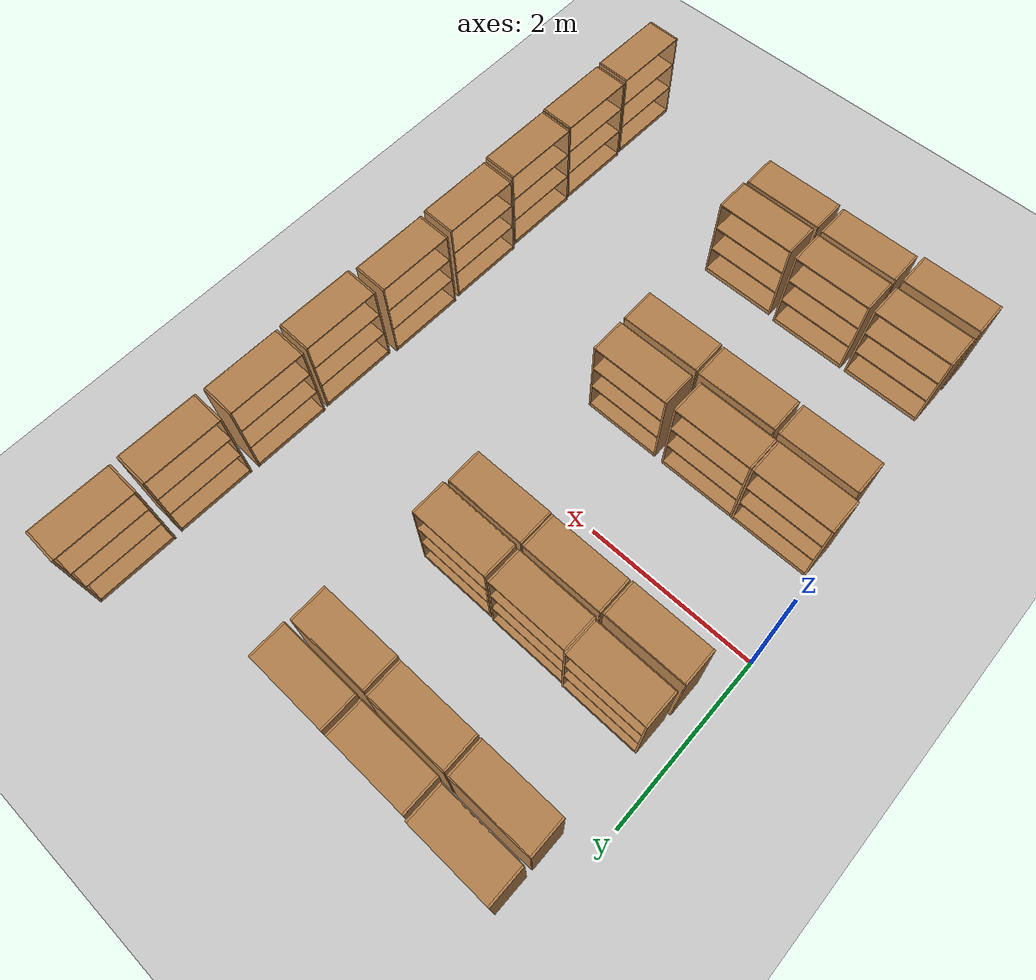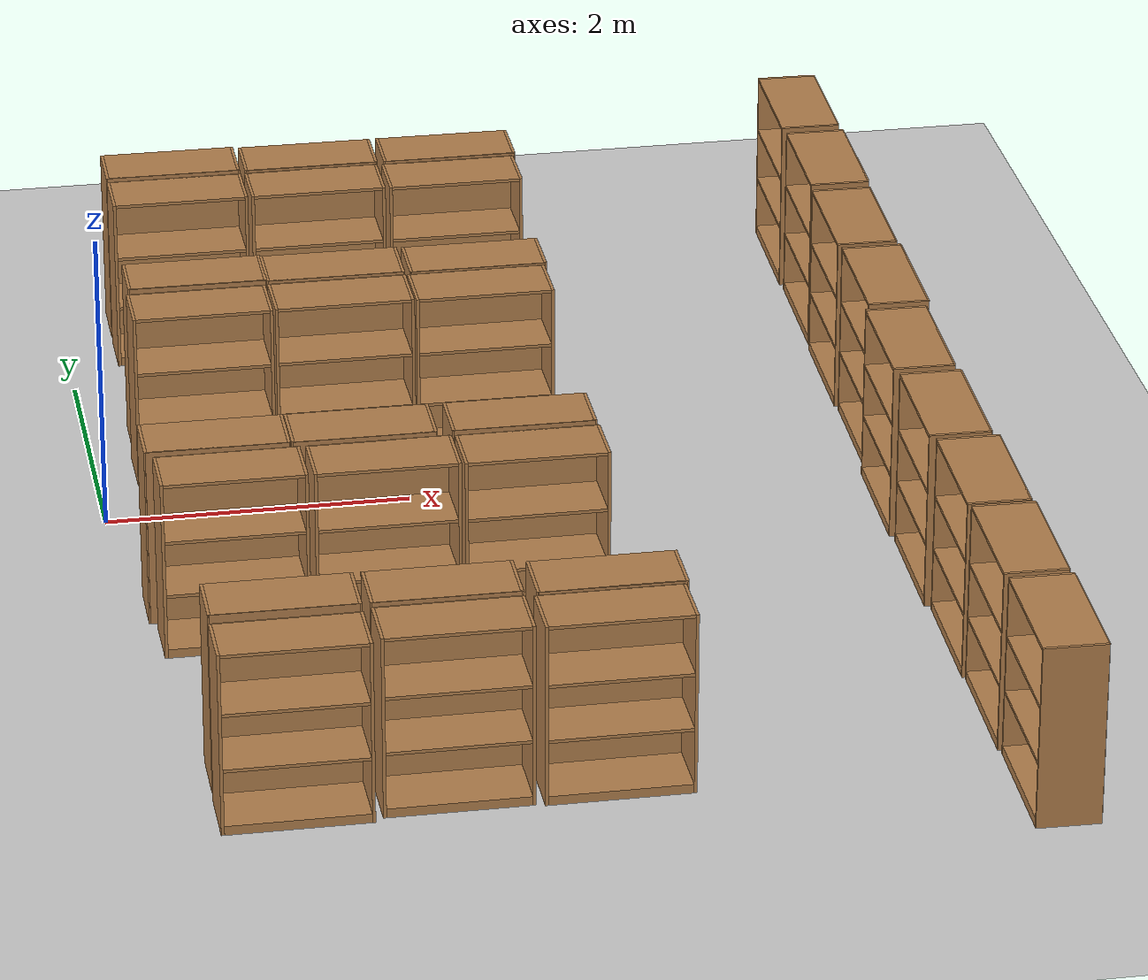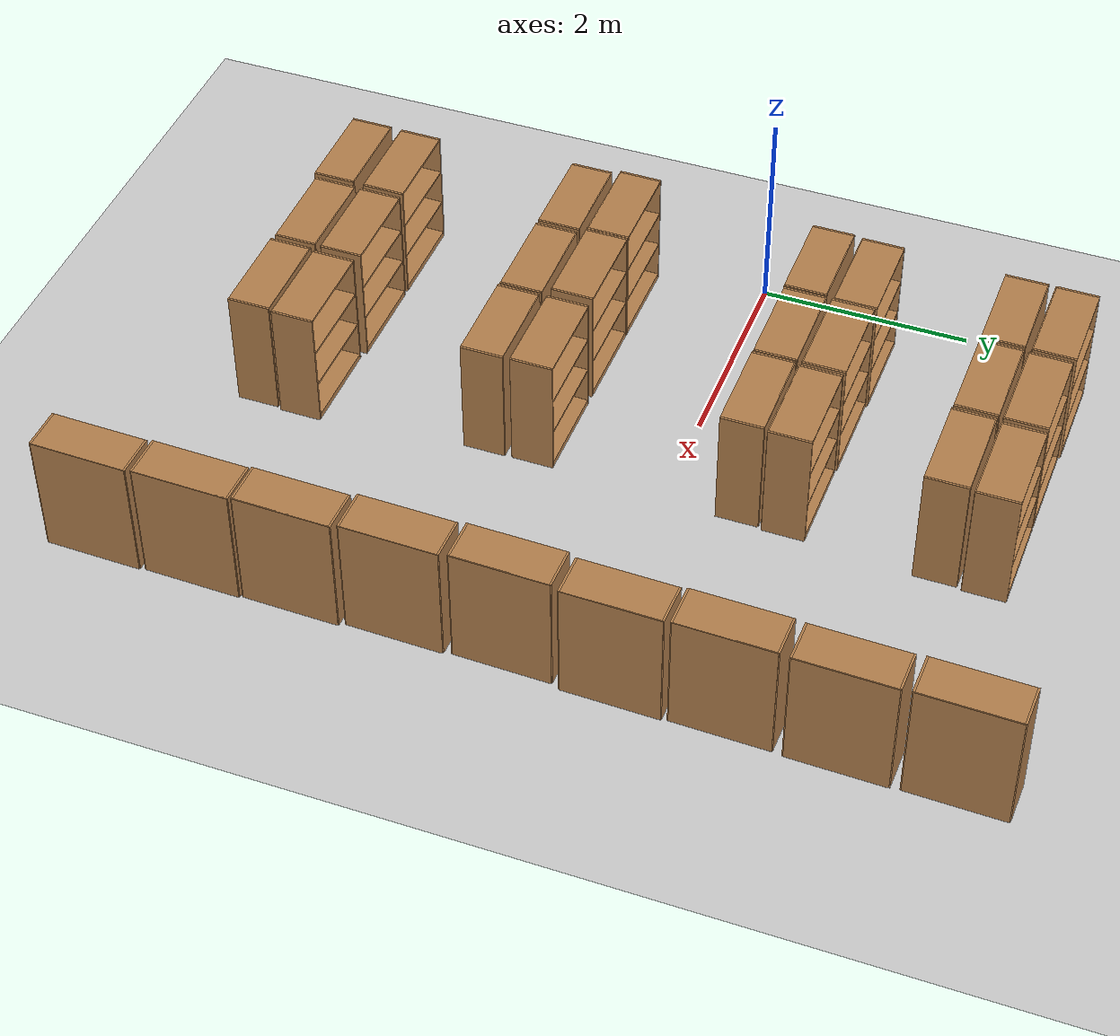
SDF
<sdf version="1.7">
 <world name="default">
  <light name="sun" type="directional">
   <pose>0 0 10 0 -0 0</pose>
   <diffuse>0.8 0.8 0.8 1</diffuse>
   <specular>0.2 0.2 0.2 1</specular>
   <attenuation>
    <range>1000</range>
    <constant>0.9</constant>
    <linear>0.01</linear>
    <quadratic>0.001</quadratic>
   </attenuation>
   <direction>-0.5 0.1 -0.9</direction>
   <spot><inner_angle>0</inner_angle><outer_angle>0</outer_angle><falloff>0</falloff></spot>
  </light>
  <model name="ground_plane">
   <static>1</static>
   <link name="link">
    <collision name="collision">
     <geometry><plane><normal>0 0 1</normal><size>100 100</size></plane></geometry>
     <surface>
      <contact><collide_bitmask>65535</collide_bitmask></contact>
      <friction><ode><mu>100</mu><mu2>50</mu2></ode></friction>
     </surface>
    </collision>
    <visual name="visual">
     <cast_shadows>0</cast_shadows>
     <geometry><plane><normal>0 0 1</normal><size>100 100</size></plane></geometry>
     <material>
      <script><uri>file://media/materials/scripts/gazebo.material</uri><name>Gazebo/Grey</name></script>
     </material>
    </visual>
   </link>
  </model>
  <gravity>0 0 -9.8</gravity>
  <magnetic_field>6e-06 2.3e-05 -4.2e-05</magnetic_field>
  <atmosphere type="adiabatic"/>
  <physics type="ode">
   <max_step_size>0.001</max_step_size>
   <real_time_factor>1</real_time_factor>
   <real_time_update_rate>1000</real_time_update_rate>
  </physics>
  <scene><ambient>0.4 0.4 0.4 1</ambient><background>0.7 0.7 0.7 1</background><shadows>1</shadows></scene>
  <audio><device>default</device></audio>
  <spherical_coordinates>
   <surface_model>EARTH_WGS84</surface_model>
   <latitude_deg>0</latitude_deg>
   <longitude_deg>0</longitude_deg>
   <elevation>0</elevation>
   <heading_deg>0</heading_deg>
  </spherical_coordinates>
  <model name="bookshelf">
   <static>1</static>
   <link name="link">
    <inertial><mass>1</mass></inertial>
    <collision name="back">
     <pose>0 0.005 0.6 0 -0 0</pose>
     <geometry><box><size>0.9 0.01 1.2</size></box></geometry>
    </collision>
    <visual name="visual1">
     <pose>0 0.005 0.6 0 -0 0</pose>
     <geometry><box><size>0.9 0.01 1.2</size></box></geometry>
     <material>
      <script><uri>file://media/materials/scripts/gazebo.material</uri><name>Gazebo/Wood</name></script>
     </material>
    </visual>
    <collision name="left_side">
     <pose>0.45 -0.195 0.6 0 -0 0</pose>
     <geometry><box><size>0.02 0.4 1.2</size></box></geometry>
    </collision>
    <visual name="visual2">
     <pose>0.45 -0.195 0.6 0 -0 0</pose>
     <geometry><box><size>0.02 0.4 1.2</size></box></geometry>
     <material>
      <script><uri>file://media/materials/scripts/gazebo.material</uri><name>Gazebo/Wood</name></script>
     </material>
    </visual>
    <collision name="right_side">
     <pose>-0.45 -0.195 0.6 0 -0 0</pose>
     <geometry><box><size>0.02 0.4 1.2</size></box></geometry>
    </collision>
    <visual name="visual3">
     <pose>-0.45 -0.195 0.6 0 -0 0</pose>
     <geometry><box><size>0.02 0.4 1.2</size></box></geometry>
     <material>
      <script><uri>file://media/materials/scripts/gazebo.material</uri><name>Gazebo/Wood</name></script>
     </material>
    </visual>
    <collision name="bottom">
     <pose>0 -0.195 0.03 0 -0 0</pose>
     <geometry><box><size>0.88 0.4 0.06</size></box></geometry>
    </collision>
    <visual name="visual4">
     <pose>0 -0.195 0.03 0 -0 0</pose>
     <geometry><box><size>0.88 0.4 0.06</size></box></geometry>
     <material>
      <script><uri>file://media/materials/scripts/gazebo.material</uri><name>Gazebo/Wood</name></script>
     </material>
    </visual>
    <collision name="top">
     <pose>0 -0.195 1.19 0 -0 0</pose>
     <geometry><box><size>0.88 0.4 0.02</size></box></geometry>
    </collision>
    <visual name="visual5">
     <pose>0 -0.195 1.19 0 -0 0</pose>
     <geometry><box><size>0.88 0.4 0.02</size></box></geometry>
     <material>
      <script><uri>file://media/materials/scripts/gazebo.material</uri><name>Gazebo/Wood</name></script>
     </material>
    </visual>
    <collision name="low_shelf">
     <pose>0 -0.195 0.43 0 -0 0</pose>
     <geometry><box><size>0.88 0.4 0.02</size></box></geometry>
    </collision>
    <visual name="visual6">
     <pose>0 -0.195 0.43 0 -0 0</pose>
     <geometry><box><size>0.88 0.4 0.02</size></box></geometry>
     <material>
      <script><uri>file://media/materials/scripts/gazebo.material</uri><name>Gazebo/Wood</name></script>
     </material>
    </visual>
    <collision name="high_shelf">
     <pose>0 -0.195 0.8 0 -0 0</pose>
     <geometry><box><size>0.88 0.4 0.02</size></box></geometry>
    </collision>
    <visual name="visual7">
     <pose>0 -0.195 0.8 0 -0 0</pose>
     <geometry><box><size>0.88 0.4 0.02</size></box></geometry>
     <material>
      <script><uri>file://media/materials/scripts/gazebo.material</uri><name>Gazebo/Wood</name></script>
     </material>
    </visual>
   </link>
   <pose>2.68648 2.72445 0 0 -0 0</pose>
  </model>
  <model name="bookshelf_0">
   <static>1</static>
   <link name="link">
    <inertial><mass>1</mass></inertial>
    <collision name="back">
     <pose>0 0.005 0.6 0 -0 0</pose>
     <geometry><box><size>0.9 0.01 1.2</size></box></geometry>
    </collision>
    <visual name="visual1">
     <pose>0 0.005 0.6 0 -0 0</pose>
     <geometry><box><size>0.9 0.01 1.2</size></box></geometry>
     <material>
      <script><uri>file://media/materials/scripts/gazebo.material</uri><name>Gazebo/Wood</name></script>
     </material>
    </visual>
    <collision name="left_side">
     <pose>0.45 -0.195 0.6 0 -0 0</pose>
     <geometry><box><size>0.02 0.4 1.2</size></box></geometry>
    </collision>
    <visual name="visual2">
     <pose>0.45 -0.195 0.6 0 -0 0</pose>
     <geometry><box><size>0.02 0.4 1.2</size></box></geometry>
     <material>
      <script><uri>file://media/materials/scripts/gazebo.material</uri><name>Gazebo/Wood</name></script>
     </material>
    </visual>
    <collision name="right_side">
     <pose>-0.45 -0.195 0.6 0 -0 0</pose>
     <geometry><box><size>0.02 0.4 1.2</size></box></geometry>
    </collision>
    <visual name="visual3">
     <pose>-0.45 -0.195 0.6 0 -0 0</pose>
     <geometry><box><size>0.02 0.4 1.2</size></box></geometry>
     <material>
      <script><uri>file://media/materials/scripts/gazebo.material</uri><name>Gazebo/Wood</name></script>
     </material>
    </visual>
    <collision name="bottom">
     <pose>0 -0.195 0.03 0 -0 0</pose>
     <geometry><box><size>0.88 0.4 0.06</size></box></geometry>
    </collision>
    <visual name="visual4">
     <pose>0 -0.195 0.03 0 -0 0</pose>
     <geometry><box><size>0.88 0.4 0.06</size></box></geometry>
     <material>
      <script><uri>file://media/materials/scripts/gazebo.material</uri><name>Gazebo/Wood</name></script>
     </material>
    </visual>
    <collision name="top">
     <pose>0 -0.195 1.19 0 -0 0</pose>
     <geometry><box><size>0.88 0.4 0.02</size></box></geometry>
    </collision>
    <visual name="visual5">
     <pose>0 -0.195 1.19 0 -0 0</pose>
     <geometry><box><size>0.88 0.4 0.02</size></box></geometry>
     <material>
      <script><uri>file://media/materials/scripts/gazebo.material</uri><name>Gazebo/Wood</name></script>
     </material>
    </visual>
    <collision name="low_shelf">
     <pose>0 -0.195 0.43 0 -0 0</pose>
     <geometry><box><size>0.88 0.4 0.02</size></box></geometry>
    </collision>
    <visual name="visual6">
     <pose>0 -0.195 0.43 0 -0 0</pose>
     <geometry><box><size>0.88 0.4 0.02</size></box></geometry>
     <material>
      <script><uri>file://media/materials/scripts/gazebo.material</uri><name>Gazebo/Wood</name></script>
     </material>
    </visual>
    <collision name="high_shelf">
     <pose>0 -0.195 0.8 0 -0 0</pose>
     <geometry><box><size>0.88 0.4 0.02</size></box></geometry>
    </collision>
    <visual name="visual7">
     <pose>0 -0.195 0.8 0 -0 0</pose>
     <geometry><box><size>0.88 0.4 0.02</size></box></geometry>
     <material>
      <script><uri>file://media/materials/scripts/gazebo.material</uri><name>Gazebo/Wood</name></script>
     </material>
    </visual>
   </link>
   <pose>1.7387 2.73379 0 0 -0 0</pose>
  </model>
  <model name="bookshelf_1">
   <static>1</static>
   <link name="link">
    <inertial><mass>1</mass></inertial>
    <collision name="back">
     <pose>0 0.005 0.6 0 -0 0</pose>
     <geometry><box><size>0.9 0.01 1.2</size></box></geometry>
    </collision>
    <visual name="visual1">
     <pose>0 0.005 0.6 0 -0 0</pose>
     <geometry><box><size>0.9 0.01 1.2</size></box></geometry>
     <material>
      <script><uri>file://media/materials/scripts/gazebo.material</uri><name>Gazebo/Wood</name></script>
     </material>
    </visual>
    <collision name="left_side">
     <pose>0.45 -0.195 0.6 0 -0 0</pose>
     <geometry><box><size>0.02 0.4 1.2</size></box></geometry>
    </collision>
    <visual name="visual2">
     <pose>0.45 -0.195 0.6 0 -0 0</pose>
     <geometry><box><size>0.02 0.4 1.2</size></box></geometry>
     <material>
      <script><uri>file://media/materials/scripts/gazebo.material</uri><name>Gazebo/Wood</name></script>
     </material>
    </visual>
    <collision name="right_side">
     <pose>-0.45 -0.195 0.6 0 -0 0</pose>
     <geometry><box><size>0.02 0.4 1.2</size></box></geometry>
    </collision>
    <visual name="visual3">
     <pose>-0.45 -0.195 0.6 0 -0 0</pose>
     <geometry><box><size>0.02 0.4 1.2</size></box></geometry>
     <material>
      <script><uri>file://media/materials/scripts/gazebo.material</uri><name>Gazebo/Wood</name></script>
     </material>
    </visual>
    <collision name="bottom">
     <pose>0 -0.195 0.03 0 -0 0</pose>
     <geometry><box><size>0.88 0.4 0.06</size></box></geometry>
    </collision>
    <visual name="visual4">
     <pose>0 -0.195 0.03 0 -0 0</pose>
     <geometry><box><size>0.88 0.4 0.06</size></box></geometry>
     <material>
      <script><uri>file://media/materials/scripts/gazebo.material</uri><name>Gazebo/Wood</name></script>
     </material>
    </visual>
    <collision name="top">
     <pose>0 -0.195 1.19 0 -0 0</pose>
     <geometry><box><size>0.88 0.4 0.02</size></box></geometry>
    </collision>
    <visual name="visual5">
     <pose>0 -0.195 1.19 0 -0 0</pose>
     <geometry><box><size>0.88 0.4 0.02</size></box></geometry>
     <material>
      <script><uri>file://media/materials/scripts/gazebo.material</uri><name>Gazebo/Wood</name></script>
     </material>
    </visual>
    <collision name="low_shelf">
     <pose>0 -0.195 0.43 0 -0 0</pose>
     <geometry><box><size>0.88 0.4 0.02</size></box></geometry>
    </collision>
    <visual name="visual6">
     <pose>0 -0.195 0.43 0 -0 0</pose>
     <geometry><box><size>0.88 0.4 0.02</size></box></geometry>
     <material>
      <script><uri>file://media/materials/scripts/gazebo.material</uri><name>Gazebo/Wood</name></script>
     </material>
    </visual>
    <collision name="high_shelf">
     <pose>0 -0.195 0.8 0 -0 0</pose>
     <geometry><box><size>0.88 0.4 0.02</size></box></geometry>
    </collision>
    <visual name="visual7">
     <pose>0 -0.195 0.8 0 -0 0</pose>
     <geometry><box><size>0.88 0.4 0.02</size></box></geometry>
     <material>
      <script><uri>file://media/materials/scripts/gazebo.material</uri><name>Gazebo/Wood</name></script>
     </material>
    </visual>
   </link>
   <pose>0.793169 2.73431 0 0 -0 0</pose>
  </model>
  <model name="bookshelf_2">
   <static>1</static>
   <link name="link">
    <inertial><mass>1</mass></inertial>
    <collision name="back">
     <pose>0 0.005 0.6 0 -0 0</pose>
     <geometry><box><size>0.9 0.01 1.2</size></box></geometry>
    </collision>
    <visual name="visual1">
     <pose>0 0.005 0.6 0 -0 0</pose>
     <geometry><box><size>0.9 0.01 1.2</size></box></geometry>
     <material>
      <script><uri>file://media/materials/scripts/gazebo.material</uri><name>Gazebo/Wood</name></script>
     </material>
    </visual>
    <collision name="left_side">
     <pose>0.45 -0.195 0.6 0 -0 0</pose>
     <geometry><box><size>0.02 0.4 1.2</size></box></geometry>
    </collision>
    <visual name="visual2">
     <pose>0.45 -0.195 0.6 0 -0 0</pose>
     <geometry><box><size>0.02 0.4 1.2</size></box></geometry>
     <material>
      <script><uri>file://media/materials/scripts/gazebo.material</uri><name>Gazebo/Wood</name></script>
     </material>
    </visual>
    <collision name="right_side">
     <pose>-0.45 -0.195 0.6 0 -0 0</pose>
     <geometry><box><size>0.02 0.4 1.2</size></box></geometry>
    </collision>
    <visual name="visual3">
     <pose>-0.45 -0.195 0.6 0 -0 0</pose>
     <geometry><box><size>0.02 0.4 1.2</size></box></geometry>
     <material>
      <script><uri>file://media/materials/scripts/gazebo.material</uri><name>Gazebo/Wood</name></script>
     </material>
    </visual>
    <collision name="bottom">
     <pose>0 -0.195 0.03 0 -0 0</pose>
     <geometry><box><size>0.88 0.4 0.06</size></box></geometry>
    </collision>
    <visual name="visual4">
     <pose>0 -0.195 0.03 0 -0 0</pose>
     <geometry><box><size>0.88 0.4 0.06</size></box></geometry>
     <material>
      <script><uri>file://media/materials/scripts/gazebo.material</uri><name>Gazebo/Wood</name></script>
     </material>
    </visual>
    <collision name="top">
     <pose>0 -0.195 1.19 0 -0 0</pose>
     <geometry><box><size>0.88 0.4 0.02</size></box></geometry>
    </collision>
    <visual name="visual5">
     <pose>0 -0.195 1.19 0 -0 0</pose>
     <geometry><box><size>0.88 0.4 0.02</size></box></geometry>
     <material>
      <script><uri>file://media/materials/scripts/gazebo.material</uri><name>Gazebo/Wood</name></script>
     </material>
    </visual>
    <collision name="low_shelf">
     <pose>0 -0.195 0.43 0 -0 0</pose>
     <geometry><box><size>0.88 0.4 0.02</size></box></geometry>
    </collision>
    <visual name="visual6">
     <pose>0 -0.195 0.43 0 -0 0</pose>
     <geometry><box><size>0.88 0.4 0.02</size></box></geometry>
     <material>
      <script><uri>file://media/materials/scripts/gazebo.material</uri><name>Gazebo/Wood</name></script>
     </material>
    </visual>
    <collision name="high_shelf">
     <pose>0 -0.195 0.8 0 -0 0</pose>
     <geometry><box><size>0.88 0.4 0.02</size></box></geometry>
    </collision>
    <visual name="visual7">
     <pose>0 -0.195 0.8 0 -0 0</pose>
     <geometry><box><size>0.88 0.4 0.02</size></box></geometry>
     <material>
      <script><uri>file://media/materials/scripts/gazebo.material</uri><name>Gazebo/Wood</name></script>
     </material>
    </visual>
   </link>
   <pose>2.61434 0.940511 0 0 -0 3.13622</pose>
  </model>
  <model name="bookshelf_2_clone">
   <static>1</static>
   <link name="link">
    <inertial><mass>1</mass></inertial>
    <collision name="back">
     <pose>0 0.005 0.6 0 -0 0</pose>
     <geometry><box><size>0.9 0.01 1.2</size></box></geometry>
    </collision>
    <visual name="visual1">
     <pose>0 0.005 0.6 0 -0 0</pose>
     <geometry><box><size>0.9 0.01 1.2</size></box></geometry>
     <material>
      <script><uri>file://media/materials/scripts/gazebo.material</uri><name>Gazebo/Wood</name></script>
     </material>
    </visual>
    <collision name="left_side">
     <pose>0.45 -0.195 0.6 0 -0 0</pose>
     <geometry><box><size>0.02 0.4 1.2</size></box></geometry>
    </collision>
    <visual name="visual2">
     <pose>0.45 -0.195 0.6 0 -0 0</pose>
     <geometry><box><size>0.02 0.4 1.2</size></box></geometry>
     <material>
      <script><uri>file://media/materials/scripts/gazebo.material</uri><name>Gazebo/Wood</name></script>
     </material>
    </visual>
    <collision name="right_side">
     <pose>-0.45 -0.195 0.6 0 -0 0</pose>
     <geometry><box><size>0.02 0.4 1.2</size></box></geometry>
    </collision>
    <visual name="visual3">
     <pose>-0.45 -0.195 0.6 0 -0 0</pose>
     <geometry><box><size>0.02 0.4 1.2</size></box></geometry>
     <material>
      <script><uri>file://media/materials/scripts/gazebo.material</uri><name>Gazebo/Wood</name></script>
     </material>
    </visual>
    <collision name="bottom">
     <pose>0 -0.195 0.03 0 -0 0</pose>
     <geometry><box><size>0.88 0.4 0.06</size></box></geometry>
    </collision>
    <visual name="visual4">
     <pose>0 -0.195 0.03 0 -0 0</pose>
     <geometry><box><size>0.88 0.4 0.06</size></box></geometry>
     <material>
      <script><uri>file://media/materials/scripts/gazebo.material</uri><name>Gazebo/Wood</name></script>
     </material>
    </visual>
    <collision name="top">
     <pose>0 -0.195 1.19 0 -0 0</pose>
     <geometry><box><size>0.88 0.4 0.02</size></box></geometry>
    </collision>
    <visual name="visual5">
     <pose>0 -0.195 1.19 0 -0 0</pose>
     <geometry><box><size>0.88 0.4 0.02</size></box></geometry>
     <material>
      <script><uri>file://media/materials/scripts/gazebo.material</uri><name>Gazebo/Wood</name></script>
     </material>
    </visual>
    <collision name="low_shelf">
     <pose>0 -0.195 0.43 0 -0 0</pose>
     <geometry><box><size>0.88 0.4 0.02</size></box></geometry>
    </collision>
    <visual name="visual6">
     <pose>0 -0.195 0.43 0 -0 0</pose>
     <geometry><box><size>0.88 0.4 0.02</size></box></geometry>
     <material>
      <script><uri>file://media/materials/scripts/gazebo.material</uri><name>Gazebo/Wood</name></script>
     </material>
    </visual>
    <collision name="high_shelf">
     <pose>0 -0.195 0.8 0 -0 0</pose>
     <geometry><box><size>0.88 0.4 0.02</size></box></geometry>
    </collision>
    <visual name="visual7">
     <pose>0 -0.195 0.8 0 -0 0</pose>
     <geometry><box><size>0.88 0.4 0.02</size></box></geometry>
     <material>
      <script><uri>file://media/materials/scripts/gazebo.material</uri><name>Gazebo/Wood</name></script>
     </material>
    </visual>
   </link>
   <pose>1.6637 0.95756 0 0 -0 3.13622</pose>
  </model>
  <model name="bookshelf_2_clone_0">
   <static>1</static>
   <link name="link">
    <inertial><mass>1</mass></inertial>
    <collision name="back">
     <pose>0 0.005 0.6 0 -0 0</pose>
     <geometry><box><size>0.9 0.01 1.2</size></box></geometry>
    </collision>
    <visual name="visual1">
     <pose>0 0.005 0.6 0 -0 0</pose>
     <geometry><box><size>0.9 0.01 1.2</size></box></geometry>
     <material>
      <script><uri>file://media/materials/scripts/gazebo.material</uri><name>Gazebo/Wood</name></script>
     </material>
    </visual>
    <collision name="left_side">
     <pose>0.45 -0.195 0.6 0 -0 0</pose>
     <geometry><box><size>0.02 0.4 1.2</size></box></geometry>
    </collision>
    <visual name="visual2">
     <pose>0.45 -0.195 0.6 0 -0 0</pose>
     <geometry><box><size>0.02 0.4 1.2</size></box></geometry>
     <material>
      <script><uri>file://media/materials/scripts/gazebo.material</uri><name>Gazebo/Wood</name></script>
     </material>
    </visual>
    <collision name="right_side">
     <pose>-0.45 -0.195 0.6 0 -0 0</pose>
     <geometry><box><size>0.02 0.4 1.2</size></box></geometry>
    </collision>
    <visual name="visual3">
     <pose>-0.45 -0.195 0.6 0 -0 0</pose>
     <geometry><box><size>0.02 0.4 1.2</size></box></geometry>
     <material>
      <script><uri>file://media/materials/scripts/gazebo.material</uri><name>Gazebo/Wood</name></script>
     </material>
    </visual>
    <collision name="bottom">
     <pose>0 -0.195 0.03 0 -0 0</pose>
     <geometry><box><size>0.88 0.4 0.06</size></box></geometry>
    </collision>
    <visual name="visual4">
     <pose>0 -0.195 0.03 0 -0 0</pose>
     <geometry><box><size>0.88 0.4 0.06</size></box></geometry>
     <material>
      <script><uri>file://media/materials/scripts/gazebo.material</uri><name>Gazebo/Wood</name></script>
     </material>
    </visual>
    <collision name="top">
     <pose>0 -0.195 1.19 0 -0 0</pose>
     <geometry><box><size>0.88 0.4 0.02</size></box></geometry>
    </collision>
    <visual name="visual5">
     <pose>0 -0.195 1.19 0 -0 0</pose>
     <geometry><box><size>0.88 0.4 0.02</size></box></geometry>
     <material>
      <script><uri>file://media/materials/scripts/gazebo.material</uri><name>Gazebo/Wood</name></script>
     </material>
    </visual>
    <collision name="low_shelf">
     <pose>0 -0.195 0.43 0 -0 0</pose>
     <geometry><box><size>0.88 0.4 0.02</size></box></geometry>
    </collision>
    <visual name="visual6">
     <pose>0 -0.195 0.43 0 -0 0</pose>
     <geometry><box><size>0.88 0.4 0.02</size></box></geometry>
     <material>
      <script><uri>file://media/materials/scripts/gazebo.material</uri><name>Gazebo/Wood</name></script>
     </material>
    </visual>
    <collision name="high_shelf">
     <pose>0 -0.195 0.8 0 -0 0</pose>
     <geometry><box><size>0.88 0.4 0.02</size></box></geometry>
    </collision>
    <visual name="visual7">
     <pose>0 -0.195 0.8 0 -0 0</pose>
     <geometry><box><size>0.88 0.4 0.02</size></box></geometry>
     <material>
      <script><uri>file://media/materials/scripts/gazebo.material</uri><name>Gazebo/Wood</name></script>
     </material>
    </visual>
   </link>
   <pose>0.747513 0.98044 0 0 -0 3.13622</pose>
  </model>
  <model name="bookshelf_clone">
   <static>1</static>
   <link name="link">
    <inertial><mass>1</mass></inertial>
    <collision name="back">
     <pose>0 0.005 0.6 0 -0 0</pose>
     <geometry><box><size>0.9 0.01 1.2</size></box></geometry>
    </collision>
    <visual name="visual1">
     <pose>0 0.005 0.6 0 -0 0</pose>
     <geometry><box><size>0.9 0.01 1.2</size></box></geometry>
     <material>
      <script><uri>file://media/materials/scripts/gazebo.material</uri><name>Gazebo/Wood</name></script>
     </material>
    </visual>
    <collision name="left_side">
     <pose>0.45 -0.195 0.6 0 -0 0</pose>
     <geometry><box><size>0.02 0.4 1.2</size></box></geometry>
    </collision>
    <visual name="visual2">
     <pose>0.45 -0.195 0.6 0 -0 0</pose>
     <geometry><box><size>0.02 0.4 1.2</size></box></geometry>
     <material>
      <script><uri>file://media/materials/scripts/gazebo.material</uri><name>Gazebo/Wood</name></script>
     </material>
    </visual>
    <collision name="right_side">
     <pose>-0.45 -0.195 0.6 0 -0 0</pose>
     <geometry><box><size>0.02 0.4 1.2</size></box></geometry>
    </collision>
    <visual name="visual3">
     <pose>-0.45 -0.195 0.6 0 -0 0</pose>
     <geometry><box><size>0.02 0.4 1.2</size></box></geometry>
     <material>
      <script><uri>file://media/materials/scripts/gazebo.material</uri><name>Gazebo/Wood</name></script>
     </material>
    </visual>
    <collision name="bottom">
     <pose>0 -0.195 0.03 0 -0 0</pose>
     <geometry><box><size>0.88 0.4 0.06</size></box></geometry>
    </collision>
    <visual name="visual4">
     <pose>0 -0.195 0.03 0 -0 0</pose>
     <geometry><box><size>0.88 0.4 0.06</size></box></geometry>
     <material>
      <script><uri>file://media/materials/scripts/gazebo.material</uri><name>Gazebo/Wood</name></script>
     </material>
    </visual>
    <collision name="top">
     <pose>0 -0.195 1.19 0 -0 0</pose>
     <geometry><box><size>0.88 0.4 0.02</size></box></geometry>
    </collision>
    <visual name="visual5">
     <pose>0 -0.195 1.19 0 -0 0</pose>
     <geometry><box><size>0.88 0.4 0.02</size></box></geometry>
     <material>
      <script><uri>file://media/materials/scripts/gazebo.material</uri><name>Gazebo/Wood</name></script>
     </material>
    </visual>
    <collision name="low_shelf">
     <pose>0 -0.195 0.43 0 -0 0</pose>
     <geometry><box><size>0.88 0.4 0.02</size></box></geometry>
    </collision>
    <visual name="visual6">
     <pose>0 -0.195 0.43 0 -0 0</pose>
     <geometry><box><size>0.88 0.4 0.02</size></box></geometry>
     <material>
      <script><uri>file://media/materials/scripts/gazebo.material</uri><name>Gazebo/Wood</name></script>
     </material>
    </visual>
    <collision name="high_shelf">
     <pose>0 -0.195 0.8 0 -0 0</pose>
     <geometry><box><size>0.88 0.4 0.02</size></box></geometry>
    </collision>
    <visual name="visual7">
     <pose>0 -0.195 0.8 0 -0 0</pose>
     <geometry><box><size>0.88 0.4 0.02</size></box></geometry>
     <material>
      <script><uri>file://media/materials/scripts/gazebo.material</uri><name>Gazebo/Wood</name></script>
     </material>
    </visual>
   </link>
   <pose>2.59058 0.88967 0 0 -0 0</pose>
  </model>
  <model name="bookshelf_clone_clone">
   <static>1</static>
   <link name="link">
    <inertial><mass>1</mass></inertial>
    <collision name="back">
     <pose>0 0.005 0.6 0 -0 0</pose>
     <geometry><box><size>0.9 0.01 1.2</size></box></geometry>
    </collision>
    <visual name="visual1">
     <pose>0 0.005 0.6 0 -0 0</pose>
     <geometry><box><size>0.9 0.01 1.2</size></box></geometry>
     <material>
      <script><uri>file://media/materials/scripts/gazebo.material</uri><name>Gazebo/Wood</name></script>
     </material>
    </visual>
    <collision name="left_side">
     <pose>0.45 -0.195 0.6 0 -0 0</pose>
     <geometry><box><size>0.02 0.4 1.2</size></box></geometry>
    </collision>
    <visual name="visual2">
     <pose>0.45 -0.195 0.6 0 -0 0</pose>
     <geometry><box><size>0.02 0.4 1.2</size></box></geometry>
     <material>
      <script><uri>file://media/materials/scripts/gazebo.material</uri><name>Gazebo/Wood</name></script>
     </material>
    </visual>
    <collision name="right_side">
     <pose>-0.45 -0.195 0.6 0 -0 0</pose>
     <geometry><box><size>0.02 0.4 1.2</size></box></geometry>
    </collision>
    <visual name="visual3">
     <pose>-0.45 -0.195 0.6 0 -0 0</pose>
     <geometry><box><size>0.02 0.4 1.2</size></box></geometry>
     <material>
      <script><uri>file://media/materials/scripts/gazebo.material</uri><name>Gazebo/Wood</name></script>
     </material>
    </visual>
    <collision name="bottom">
     <pose>0 -0.195 0.03 0 -0 0</pose>
     <geometry><box><size>0.88 0.4 0.06</size></box></geometry>
    </collision>
    <visual name="visual4">
     <pose>0 -0.195 0.03 0 -0 0</pose>
     <geometry><box><size>0.88 0.4 0.06</size></box></geometry>
     <material>
      <script><uri>file://media/materials/scripts/gazebo.material</uri><name>Gazebo/Wood</name></script>
     </material>
    </visual>
    <collision name="top">
     <pose>0 -0.195 1.19 0 -0 0</pose>
     <geometry><box><size>0.88 0.4 0.02</size></box></geometry>
    </collision>
    <visual name="visual5">
     <pose>0 -0.195 1.19 0 -0 0</pose>
     <geometry><box><size>0.88 0.4 0.02</size></box></geometry>
     <material>
      <script><uri>file://media/materials/scripts/gazebo.material</uri><name>Gazebo/Wood</name></script>
     </material>
    </visual>
    <collision name="low_shelf">
     <pose>0 -0.195 0.43 0 -0 0</pose>
     <geometry><box><size>0.88 0.4 0.02</size></box></geometry>
    </collision>
    <visual name="visual6">
     <pose>0 -0.195 0.43 0 -0 0</pose>
     <geometry><box><size>0.88 0.4 0.02</size></box></geometry>
     <material>
      <script><uri>file://media/materials/scripts/gazebo.material</uri><name>Gazebo/Wood</name></script>
     </material>
    </visual>
    <collision name="high_shelf">
     <pose>0 -0.195 0.8 0 -0 0</pose>
     <geometry><box><size>0.88 0.4 0.02</size></box></geometry>
    </collision>
    <visual name="visual7">
     <pose>0 -0.195 0.8 0 -0 0</pose>
     <geometry><box><size>0.88 0.4 0.02</size></box></geometry>
     <material>
      <script><uri>file://media/materials/scripts/gazebo.material</uri><name>Gazebo/Wood</name></script>
     </material>
    </visual>
   </link>
   <pose>1.6608 0.896396 0 0 -0 0</pose>
  </model>
  <model name="bookshelf_clone_clone_clone">
   <static>1</static>
   <link name="link">
    <inertial><mass>1</mass></inertial>
    <collision name="back">
     <pose>0 0.005 0.6 0 -0 0</pose>
     <geometry><box><size>0.9 0.01 1.2</size></box></geometry>
    </collision>
    <visual name="visual1">
     <pose>0 0.005 0.6 0 -0 0</pose>
     <geometry><box><size>0.9 0.01 1.2</size></box></geometry>
     <material>
      <script><uri>file://media/materials/scripts/gazebo.material</uri><name>Gazebo/Wood</name></script>
     </material>
    </visual>
    <collision name="left_side">
     <pose>0.45 -0.195 0.6 0 -0 0</pose>
     <geometry><box><size>0.02 0.4 1.2</size></box></geometry>
    </collision>
    <visual name="visual2">
     <pose>0.45 -0.195 0.6 0 -0 0</pose>
     <geometry><box><size>0.02 0.4 1.2</size></box></geometry>
     <material>
      <script><uri>file://media/materials/scripts/gazebo.material</uri><name>Gazebo/Wood</name></script>
     </material>
    </visual>
    <collision name="right_side">
     <pose>-0.45 -0.195 0.6 0 -0 0</pose>
     <geometry><box><size>0.02 0.4 1.2</size></box></geometry>
    </collision>
    <visual name="visual3">
     <pose>-0.45 -0.195 0.6 0 -0 0</pose>
     <geometry><box><size>0.02 0.4 1.2</size></box></geometry>
     <material>
      <script><uri>file://media/materials/scripts/gazebo.material</uri><name>Gazebo/Wood</name></script>
     </material>
    </visual>
    <collision name="bottom">
     <pose>0 -0.195 0.03 0 -0 0</pose>
     <geometry><box><size>0.88 0.4 0.06</size></box></geometry>
    </collision>
    <visual name="visual4">
     <pose>0 -0.195 0.03 0 -0 0</pose>
     <geometry><box><size>0.88 0.4 0.06</size></box></geometry>
     <material>
      <script><uri>file://media/materials/scripts/gazebo.material</uri><name>Gazebo/Wood</name></script>
     </material>
    </visual>
    <collision name="top">
     <pose>0 -0.195 1.19 0 -0 0</pose>
     <geometry><box><size>0.88 0.4 0.02</size></box></geometry>
    </collision>
    <visual name="visual5">
     <pose>0 -0.195 1.19 0 -0 0</pose>
     <geometry><box><size>0.88 0.4 0.02</size></box></geometry>
     <material>
      <script><uri>file://media/materials/scripts/gazebo.material</uri><name>Gazebo/Wood</name></script>
     </material>
    </visual>
    <collision name="low_shelf">
     <pose>0 -0.195 0.43 0 -0 0</pose>
     <geometry><box><size>0.88 0.4 0.02</size></box></geometry>
    </collision>
    <visual name="visual6">
     <pose>0 -0.195 0.43 0 -0 0</pose>
     <geometry><box><size>0.88 0.4 0.02</size></box></geometry>
     <material>
      <script><uri>file://media/materials/scripts/gazebo.material</uri><name>Gazebo/Wood</name></script>
     </material>
    </visual>
    <collision name="high_shelf">
     <pose>0 -0.195 0.8 0 -0 0</pose>
     <geometry><box><size>0.88 0.4 0.02</size></box></geometry>
    </collision>
    <visual name="visual7">
     <pose>0 -0.195 0.8 0 -0 0</pose>
     <geometry><box><size>0.88 0.4 0.02</size></box></geometry>
     <material>
      <script><uri>file://media/materials/scripts/gazebo.material</uri><name>Gazebo/Wood</name></script>
     </material>
    </visual>
   </link>
   <pose>0.72663 0.888413 0 0 -0 0</pose>
  </model>
  <model name="bookshelf_2_clone_0_clone">
   <static>1</static>
   <link name="link">
    <inertial><mass>1</mass></inertial>
    <collision name="back">
     <pose>0 0.005 0.6 0 -0 0</pose>
     <geometry><box><size>0.9 0.01 1.2</size></box></geometry>
    </collision>
    <visual name="visual1">
     <pose>0 0.005 0.6 0 -0 0</pose>
     <geometry><box><size>0.9 0.01 1.2</size></box></geometry>
     <material>
      <script><uri>file://media/materials/scripts/gazebo.material</uri><name>Gazebo/Wood</name></script>
     </material>
    </visual>
    <collision name="left_side">
     <pose>0.45 -0.195 0.6 0 -0 0</pose>
     <geometry><box><size>0.02 0.4 1.2</size></box></geometry>
    </collision>
    <visual name="visual2">
     <pose>0.45 -0.195 0.6 0 -0 0</pose>
     <geometry><box><size>0.02 0.4 1.2</size></box></geometry>
     <material>
      <script><uri>file://media/materials/scripts/gazebo.material</uri><name>Gazebo/Wood</name></script>
     </material>
    </visual>
    <collision name="right_side">
     <pose>-0.45 -0.195 0.6 0 -0 0</pose>
     <geometry><box><size>0.02 0.4 1.2</size></box></geometry>
    </collision>
    <visual name="visual3">
     <pose>-0.45 -0.195 0.6 0 -0 0</pose>
     <geometry><box><size>0.02 0.4 1.2</size></box></geometry>
     <material>
      <script><uri>file://media/materials/scripts/gazebo.material</uri><name>Gazebo/Wood</name></script>
     </material>
    </visual>
    <collision name="bottom">
     <pose>0 -0.195 0.03 0 -0 0</pose>
     <geometry><box><size>0.88 0.4 0.06</size></box></geometry>
    </collision>
    <visual name="visual4">
     <pose>0 -0.195 0.03 0 -0 0</pose>
     <geometry><box><size>0.88 0.4 0.06</size></box></geometry>
     <material>
      <script><uri>file://media/materials/scripts/gazebo.material</uri><name>Gazebo/Wood</name></script>
     </material>
    </visual>
    <collision name="top">
     <pose>0 -0.195 1.19 0 -0 0</pose>
     <geometry><box><size>0.88 0.4 0.02</size></box></geometry>
    </collision>
    <visual name="visual5">
     <pose>0 -0.195 1.19 0 -0 0</pose>
     <geometry><box><size>0.88 0.4 0.02</size></box></geometry>
     <material>
      <script><uri>file://media/materials/scripts/gazebo.material</uri><name>Gazebo/Wood</name></script>
     </material>
    </visual>
    <collision name="low_shelf">
     <pose>0 -0.195 0.43 0 -0 0</pose>
     <geometry><box><size>0.88 0.4 0.02</size></box></geometry>
    </collision>
    <visual name="visual6">
     <pose>0 -0.195 0.43 0 -0 0</pose>
     <geometry><box><size>0.88 0.4 0.02</size></box></geometry>
     <material>
      <script><uri>file://media/materials/scripts/gazebo.material</uri><name>Gazebo/Wood</name></script>
     </material>
    </visual>
    <collision name="high_shelf">
     <pose>0 -0.195 0.8 0 -0 0</pose>
     <geometry><box><size>0.88 0.4 0.02</size></box></geometry>
    </collision>
    <visual name="visual7">
     <pose>0 -0.195 0.8 0 -0 0</pose>
     <geometry><box><size>0.88 0.4 0.02</size></box></geometry>
     <material>
      <script><uri>file://media/materials/scripts/gazebo.material</uri><name>Gazebo/Wood</name></script>
     </material>
    </visual>
   </link>
   <pose>2.71065 2.78539 0 0 -0 3.13622</pose>
  </model>
  <model name="bookshelf_2_clone_0_clone_0">
   <static>1</static>
   <link name="link">
    <inertial><mass>1</mass></inertial>
    <collision name="back">
     <pose>0 0.005 0.6 0 -0 0</pose>
     <geometry><box><size>0.9 0.01 1.2</size></box></geometry>
    </collision>
    <visual name="visual1">
     <pose>0 0.005 0.6 0 -0 0</pose>
     <geometry><box><size>0.9 0.01 1.2</size></box></geometry>
     <material>
      <script><uri>file://media/materials/scripts/gazebo.material</uri><name>Gazebo/Wood</name></script>
     </material>
    </visual>
    <collision name="left_side">
     <pose>0.45 -0.195 0.6 0 -0 0</pose>
     <geometry><box><size>0.02 0.4 1.2</size></box></geometry>
    </collision>
    <visual name="visual2">
     <pose>0.45 -0.195 0.6 0 -0 0</pose>
     <geometry><box><size>0.02 0.4 1.2</size></box></geometry>
     <material>
      <script><uri>file://media/materials/scripts/gazebo.material</uri><name>Gazebo/Wood</name></script>
     </material>
    </visual>
    <collision name="right_side">
     <pose>-0.45 -0.195 0.6 0 -0 0</pose>
     <geometry><box><size>0.02 0.4 1.2</size></box></geometry>
    </collision>
    <visual name="visual3">
     <pose>-0.45 -0.195 0.6 0 -0 0</pose>
     <geometry><box><size>0.02 0.4 1.2</size></box></geometry>
     <material>
      <script><uri>file://media/materials/scripts/gazebo.material</uri><name>Gazebo/Wood</name></script>
     </material>
    </visual>
    <collision name="bottom">
     <pose>0 -0.195 0.03 0 -0 0</pose>
     <geometry><box><size>0.88 0.4 0.06</size></box></geometry>
    </collision>
    <visual name="visual4">
     <pose>0 -0.195 0.03 0 -0 0</pose>
     <geometry><box><size>0.88 0.4 0.06</size></box></geometry>
     <material>
      <script><uri>file://media/materials/scripts/gazebo.material</uri><name>Gazebo/Wood</name></script>
     </material>
    </visual>
    <collision name="top">
     <pose>0 -0.195 1.19 0 -0 0</pose>
     <geometry><box><size>0.88 0.4 0.02</size></box></geometry>
    </collision>
    <visual name="visual5">
     <pose>0 -0.195 1.19 0 -0 0</pose>
     <geometry><box><size>0.88 0.4 0.02</size></box></geometry>
     <material>
      <script><uri>file://media/materials/scripts/gazebo.material</uri><name>Gazebo/Wood</name></script>
     </material>
    </visual>
    <collision name="low_shelf">
     <pose>0 -0.195 0.43 0 -0 0</pose>
     <geometry><box><size>0.88 0.4 0.02</size></box></geometry>
    </collision>
    <visual name="visual6">
     <pose>0 -0.195 0.43 0 -0 0</pose>
     <geometry><box><size>0.88 0.4 0.02</size></box></geometry>
     <material>
      <script><uri>file://media/materials/scripts/gazebo.material</uri><name>Gazebo/Wood</name></script>
     </material>
    </visual>
    <collision name="high_shelf">
     <pose>0 -0.195 0.8 0 -0 0</pose>
     <geometry><box><size>0.88 0.4 0.02</size></box></geometry>
    </collision>
    <visual name="visual7">
     <pose>0 -0.195 0.8 0 -0 0</pose>
     <geometry><box><size>0.88 0.4 0.02</size></box></geometry>
     <material>
      <script><uri>file://media/materials/scripts/gazebo.material</uri><name>Gazebo/Wood</name></script>
     </material>
    </visual>
   </link>
   <pose>1.74885 2.78963 0 0 -0 3.13622</pose>
  </model>
  <model name="bookshelf_2_clone_0_clone_1">
   <static>1</static>
   <link name="link">
    <inertial><mass>1</mass></inertial>
    <collision name="back">
     <pose>0 0.005 0.6 0 -0 0</pose>
     <geometry><box><size>0.9 0.01 1.2</size></box></geometry>
    </collision>
    <visual name="visual1">
     <pose>0 0.005 0.6 0 -0 0</pose>
     <geometry><box><size>0.9 0.01 1.2</size></box></geometry>
     <material>
      <script><uri>file://media/materials/scripts/gazebo.material</uri><name>Gazebo/Wood</name></script>
     </material>
    </visual>
    <collision name="left_side">
     <pose>0.45 -0.195 0.6 0 -0 0</pose>
     <geometry><box><size>0.02 0.4 1.2</size></box></geometry>
    </collision>
    <visual name="visual2">
     <pose>0.45 -0.195 0.6 0 -0 0</pose>
     <geometry><box><size>0.02 0.4 1.2</size></box></geometry>
     <material>
      <script><uri>file://media/materials/scripts/gazebo.material</uri><name>Gazebo/Wood</name></script>
     </material>
    </visual>
    <collision name="right_side">
     <pose>-0.45 -0.195 0.6 0 -0 0</pose>
     <geometry><box><size>0.02 0.4 1.2</size></box></geometry>
    </collision>
    <visual name="visual3">
     <pose>-0.45 -0.195 0.6 0 -0 0</pose>
     <geometry><box><size>0.02 0.4 1.2</size></box></geometry>
     <material>
      <script><uri>file://media/materials/scripts/gazebo.material</uri><name>Gazebo/Wood</name></script>
     </material>
    </visual>
    <collision name="bottom">
     <pose>0 -0.195 0.03 0 -0 0</pose>
     <geometry><box><size>0.88 0.4 0.06</size></box></geometry>
    </collision>
    <visual name="visual4">
     <pose>0 -0.195 0.03 0 -0 0</pose>
     <geometry><box><size>0.88 0.4 0.06</size></box></geometry>
     <material>
      <script><uri>file://media/materials/scripts/gazebo.material</uri><name>Gazebo/Wood</name></script>
     </material>
    </visual>
    <collision name="top">
     <pose>0 -0.195 1.19 0 -0 0</pose>
     <geometry><box><size>0.88 0.4 0.02</size></box></geometry>
    </collision>
    <visual name="visual5">
     <pose>0 -0.195 1.19 0 -0 0</pose>
     <geometry><box><size>0.88 0.4 0.02</size></box></geometry>
     <material>
      <script><uri>file://media/materials/scripts/gazebo.material</uri><name>Gazebo/Wood</name></script>
     </material>
    </visual>
    <collision name="low_shelf">
     <pose>0 -0.195 0.43 0 -0 0</pose>
     <geometry><box><size>0.88 0.4 0.02</size></box></geometry>
    </collision>
    <visual name="visual6">
     <pose>0 -0.195 0.43 0 -0 0</pose>
     <geometry><box><size>0.88 0.4 0.02</size></box></geometry>
     <material>
      <script><uri>file://media/materials/scripts/gazebo.material</uri><name>Gazebo/Wood</name></script>
     </material>
    </visual>
    <collision name="high_shelf">
     <pose>0 -0.195 0.8 0 -0 0</pose>
     <geometry><box><size>0.88 0.4 0.02</size></box></geometry>
    </collision>
    <visual name="visual7">
     <pose>0 -0.195 0.8 0 -0 0</pose>
     <geometry><box><size>0.88 0.4 0.02</size></box></geometry>
     <material>
      <script><uri>file://media/materials/scripts/gazebo.material</uri><name>Gazebo/Wood</name></script>
     </material>
    </visual>
   </link>
   <pose>0.795432 2.81359 0 0 -0 3.13622</pose>
  </model>
  <model name="bookshelf_2_clone_1">
   <static>1</static>
   <link name="link">
    <inertial><mass>1</mass></inertial>
    <collision name="back">
     <pose>0 0.005 0.6 0 -0 0</pose>
     <geometry><box><size>0.9 0.01 1.2</size></box></geometry>
    </collision>
    <visual name="visual1">
     <pose>0 0.005 0.6 0 -0 0</pose>
     <geometry><box><size>0.9 0.01 1.2</size></box></geometry>
     <material>
      <script><uri>file://media/materials/scripts/gazebo.material</uri><name>Gazebo/Wood</name></script>
     </material>
    </visual>
    <collision name="left_side">
     <pose>0.45 -0.195 0.6 0 -0 0</pose>
     <geometry><box><size>0.02 0.4 1.2</size></box></geometry>
    </collision>
    <visual name="visual2">
     <pose>0.45 -0.195 0.6 0 -0 0</pose>
     <geometry><box><size>0.02 0.4 1.2</size></box></geometry>
     <material>
      <script><uri>file://media/materials/scripts/gazebo.material</uri><name>Gazebo/Wood</name></script>
     </material>
    </visual>
    <collision name="right_side">
     <pose>-0.45 -0.195 0.6 0 -0 0</pose>
     <geometry><box><size>0.02 0.4 1.2</size></box></geometry>
    </collision>
    <visual name="visual3">
     <pose>-0.45 -0.195 0.6 0 -0 0</pose>
     <geometry><box><size>0.02 0.4 1.2</size></box></geometry>
     <material>
      <script><uri>file://media/materials/scripts/gazebo.material</uri><name>Gazebo/Wood</name></script>
     </material>
    </visual>
    <collision name="bottom">
     <pose>0 -0.195 0.03 0 -0 0</pose>
     <geometry><box><size>0.88 0.4 0.06</size></box></geometry>
    </collision>
    <visual name="visual4">
     <pose>0 -0.195 0.03 0 -0 0</pose>
     <geometry><box><size>0.88 0.4 0.06</size></box></geometry>
     <material>
      <script><uri>file://media/materials/scripts/gazebo.material</uri><name>Gazebo/Wood</name></script>
     </material>
    </visual>
    <collision name="top">
     <pose>0 -0.195 1.19 0 -0 0</pose>
     <geometry><box><size>0.88 0.4 0.02</size></box></geometry>
    </collision>
    <visual name="visual5">
     <pose>0 -0.195 1.19 0 -0 0</pose>
     <geometry><box><size>0.88 0.4 0.02</size></box></geometry>
     <material>
      <script><uri>file://media/materials/scripts/gazebo.material</uri><name>Gazebo/Wood</name></script>
     </material>
    </visual>
    <collision name="low_shelf">
     <pose>0 -0.195 0.43 0 -0 0</pose>
     <geometry><box><size>0.88 0.4 0.02</size></box></geometry>
    </collision>
    <visual name="visual6">
     <pose>0 -0.195 0.43 0 -0 0</pose>
     <geometry><box><size>0.88 0.4 0.02</size></box></geometry>
     <material>
      <script><uri>file://media/materials/scripts/gazebo.material</uri><name>Gazebo/Wood</name></script>
     </material>
    </visual>
    <collision name="high_shelf">
     <pose>0 -0.195 0.8 0 -0 0</pose>
     <geometry><box><size>0.88 0.4 0.02</size></box></geometry>
    </collision>
    <visual name="visual7">
     <pose>0 -0.195 0.8 0 -0 0</pose>
     <geometry><box><size>0.88 0.4 0.02</size></box></geometry>
     <material>
      <script><uri>file://media/materials/scripts/gazebo.material</uri><name>Gazebo/Wood</name></script>
     </material>
    </visual>
   </link>
   <pose>2.51878 -1.46416 0 0 -0 3.13622</pose>
  </model>
  <model name="bookshelf_2_clone_2">
   <static>1</static>
   <link name="link">
    <inertial><mass>1</mass></inertial>
    <collision name="back">
     <pose>0 0.005 0.6 0 -0 0</pose>
     <geometry><box><size>0.9 0.01 1.2</size></box></geometry>
    </collision>
    <visual name="visual1">
     <pose>0 0.005 0.6 0 -0 0</pose>
     <geometry><box><size>0.9 0.01 1.2</size></box></geometry>
     <material>
      <script><uri>file://media/materials/scripts/gazebo.material</uri><name>Gazebo/Wood</name></script>
     </material>
    </visual>
    <collision name="left_side">
     <pose>0.45 -0.195 0.6 0 -0 0</pose>
     <geometry><box><size>0.02 0.4 1.2</size></box></geometry>
    </collision>
    <visual name="visual2">
     <pose>0.45 -0.195 0.6 0 -0 0</pose>
     <geometry><box><size>0.02 0.4 1.2</size></box></geometry>
     <material>
      <script><uri>file://media/materials/scripts/gazebo.material</uri><name>Gazebo/Wood</name></script>
     </material>
    </visual>
    <collision name="right_side">
     <pose>-0.45 -0.195 0.6 0 -0 0</pose>
     <geometry><box><size>0.02 0.4 1.2</size></box></geometry>
    </collision>
    <visual name="visual3">
     <pose>-0.45 -0.195 0.6 0 -0 0</pose>
     <geometry><box><size>0.02 0.4 1.2</size></box></geometry>
     <material>
      <script><uri>file://media/materials/scripts/gazebo.material</uri><name>Gazebo/Wood</name></script>
     </material>
    </visual>
    <collision name="bottom">
     <pose>0 -0.195 0.03 0 -0 0</pose>
     <geometry><box><size>0.88 0.4 0.06</size></box></geometry>
    </collision>
    <visual name="visual4">
     <pose>0 -0.195 0.03 0 -0 0</pose>
     <geometry><box><size>0.88 0.4 0.06</size></box></geometry>
     <material>
      <script><uri>file://media/materials/scripts/gazebo.material</uri><name>Gazebo/Wood</name></script>
     </material>
    </visual>
    <collision name="top">
     <pose>0 -0.195 1.19 0 -0 0</pose>
     <geometry><box><size>0.88 0.4 0.02</size></box></geometry>
    </collision>
    <visual name="visual5">
     <pose>0 -0.195 1.19 0 -0 0</pose>
     <geometry><box><size>0.88 0.4 0.02</size></box></geometry>
     <material>
      <script><uri>file://media/materials/scripts/gazebo.material</uri><name>Gazebo/Wood</name></script>
     </material>
    </visual>
    <collision name="low_shelf">
     <pose>0 -0.195 0.43 0 -0 0</pose>
     <geometry><box><size>0.88 0.4 0.02</size></box></geometry>
    </collision>
    <visual name="visual6">
     <pose>0 -0.195 0.43 0 -0 0</pose>
     <geometry><box><size>0.88 0.4 0.02</size></box></geometry>
     <material>
      <script><uri>file://media/materials/scripts/gazebo.material</uri><name>Gazebo/Wood</name></script>
     </material>
    </visual>
    <collision name="high_shelf">
     <pose>0 -0.195 0.8 0 -0 0</pose>
     <geometry><box><size>0.88 0.4 0.02</size></box></geometry>
    </collision>
    <visual name="visual7">
     <pose>0 -0.195 0.8 0 -0 0</pose>
     <geometry><box><size>0.88 0.4 0.02</size></box></geometry>
     <material>
      <script><uri>file://media/materials/scripts/gazebo.material</uri><name>Gazebo/Wood</name></script>
     </material>
    </visual>
   </link>
   <pose>1.50781 -1.45641 0 0 -0 3.13622</pose>
  </model>
  <model name="bookshelf_2_clone_3">
   <static>1</static>
   <link name="link">
    <inertial><mass>1</mass></inertial>
    <collision name="back">
     <pose>0 0.005 0.6 0 -0 0</pose>
     <geometry><box><size>0.9 0.01 1.2</size></box></geometry>
    </collision>
    <visual name="visual1">
     <pose>0 0.005 0.6 0 -0 0</pose>
     <geometry><box><size>0.9 0.01 1.2</size></box></geometry>
     <material>
      <script><uri>file://media/materials/scripts/gazebo.material</uri><name>Gazebo/Wood</name></script>
     </material>
    </visual>
    <collision name="left_side">
     <pose>0.45 -0.195 0.6 0 -0 0</pose>
     <geometry><box><size>0.02 0.4 1.2</size></box></geometry>
    </collision>
    <visual name="visual2">
     <pose>0.45 -0.195 0.6 0 -0 0</pose>
     <geometry><box><size>0.02 0.4 1.2</size></box></geometry>
     <material>
      <script><uri>file://media/materials/scripts/gazebo.material</uri><name>Gazebo/Wood</name></script>
     </material>
    </visual>
    <collision name="right_side">
     <pose>-0.45 -0.195 0.6 0 -0 0</pose>
     <geometry><box><size>0.02 0.4 1.2</size></box></geometry>
    </collision>
    <visual name="visual3">
     <pose>-0.45 -0.195 0.6 0 -0 0</pose>
     <geometry><box><size>0.02 0.4 1.2</size></box></geometry>
     <material>
      <script><uri>file://media/materials/scripts/gazebo.material</uri><name>Gazebo/Wood</name></script>
     </material>
    </visual>
    <collision name="bottom">
     <pose>0 -0.195 0.03 0 -0 0</pose>
     <geometry><box><size>0.88 0.4 0.06</size></box></geometry>
    </collision>
    <visual name="visual4">
     <pose>0 -0.195 0.03 0 -0 0</pose>
     <geometry><box><size>0.88 0.4 0.06</size></box></geometry>
     <material>
      <script><uri>file://media/materials/scripts/gazebo.material</uri><name>Gazebo/Wood</name></script>
     </material>
    </visual>
    <collision name="top">
     <pose>0 -0.195 1.19 0 -0 0</pose>
     <geometry><box><size>0.88 0.4 0.02</size></box></geometry>
    </collision>
    <visual name="visual5">
     <pose>0 -0.195 1.19 0 -0 0</pose>
     <geometry><box><size>0.88 0.4 0.02</size></box></geometry>
     <material>
      <script><uri>file://media/materials/scripts/gazebo.material</uri><name>Gazebo/Wood</name></script>
     </material>
    </visual>
    <collision name="low_shelf">
     <pose>0 -0.195 0.43 0 -0 0</pose>
     <geometry><box><size>0.88 0.4 0.02</size></box></geometry>
    </collision>
    <visual name="visual6">
     <pose>0 -0.195 0.43 0 -0 0</pose>
     <geometry><box><size>0.88 0.4 0.02</size></box></geometry>
     <material>
      <script><uri>file://media/materials/scripts/gazebo.material</uri><name>Gazebo/Wood</name></script>
     </material>
    </visual>
    <collision name="high_shelf">
     <pose>0 -0.195 0.8 0 -0 0</pose>
     <geometry><box><size>0.88 0.4 0.02</size></box></geometry>
    </collision>
    <visual name="visual7">
     <pose>0 -0.195 0.8 0 -0 0</pose>
     <geometry><box><size>0.88 0.4 0.02</size></box></geometry>
     <material>
      <script><uri>file://media/materials/scripts/gazebo.material</uri><name>Gazebo/Wood</name></script>
     </material>
    </visual>
   </link>
   <pose>0.583819 -1.44906 0 0 -0 3.13622</pose>
  </model>
  <model name="bookshelf_clone_clone_0">
   <static>1</static>
   <link name="link">
    <inertial><mass>1</mass></inertial>
    <collision name="back">
     <pose>0 0.005 0.6 0 -0 0</pose>
     <geometry><box><size>0.9 0.01 1.2</size></box></geometry>
    </collision>
    <visual name="visual1">
     <pose>0 0.005 0.6 0 -0 0</pose>
     <geometry><box><size>0.9 0.01 1.2</size></box></geometry>
     <material>
      <script><uri>file://media/materials/scripts/gazebo.material</uri><name>Gazebo/Wood</name></script>
     </material>
    </visual>
    <collision name="left_side">
     <pose>0.45 -0.195 0.6 0 -0 0</pose>
     <geometry><box><size>0.02 0.4 1.2</size></box></geometry>
    </collision>
    <visual name="visual2">
     <pose>0.45 -0.195 0.6 0 -0 0</pose>
     <geometry><box><size>0.02 0.4 1.2</size></box></geometry>
     <material>
      <script><uri>file://media/materials/scripts/gazebo.material</uri><name>Gazebo/Wood</name></script>
     </material>
    </visual>
    <collision name="right_side">
     <pose>-0.45 -0.195 0.6 0 -0 0</pose>
     <geometry><box><size>0.02 0.4 1.2</size></box></geometry>
    </collision>
    <visual name="visual3">
     <pose>-0.45 -0.195 0.6 0 -0 0</pose>
     <geometry><box><size>0.02 0.4 1.2</size></box></geometry>
     <material>
      <script><uri>file://media/materials/scripts/gazebo.material</uri><name>Gazebo/Wood</name></script>
     </material>
    </visual>
    <collision name="bottom">
     <pose>0 -0.195 0.03 0 -0 0</pose>
     <geometry><box><size>0.88 0.4 0.06</size></box></geometry>
    </collision>
    <visual name="visual4">
     <pose>0 -0.195 0.03 0 -0 0</pose>
     <geometry><box><size>0.88 0.4 0.06</size></box></geometry>
     <material>
      <script><uri>file://media/materials/scripts/gazebo.material</uri><name>Gazebo/Wood</name></script>
     </material>
    </visual>
    <collision name="top">
     <pose>0 -0.195 1.19 0 -0 0</pose>
     <geometry><box><size>0.88 0.4 0.02</size></box></geometry>
    </collision>
    <visual name="visual5">
     <pose>0 -0.195 1.19 0 -0 0</pose>
     <geometry><box><size>0.88 0.4 0.02</size></box></geometry>
     <material>
      <script><uri>file://media/materials/scripts/gazebo.material</uri><name>Gazebo/Wood</name></script>
     </material>
    </visual>
    <collision name="low_shelf">
     <pose>0 -0.195 0.43 0 -0 0</pose>
     <geometry><box><size>0.88 0.4 0.02</size></box></geometry>
    </collision>
    <visual name="visual6">
     <pose>0 -0.195 0.43 0 -0 0</pose>
     <geometry><box><size>0.88 0.4 0.02</size></box></geometry>
     <material>
      <script><uri>file://media/materials/scripts/gazebo.material</uri><name>Gazebo/Wood</name></script>
     </material>
    </visual>
    <collision name="high_shelf">
     <pose>0 -0.195 0.8 0 -0 0</pose>
     <geometry><box><size>0.88 0.4 0.02</size></box></geometry>
    </collision>
    <visual name="visual7">
     <pose>0 -0.195 0.8 0 -0 0</pose>
     <geometry><box><size>0.88 0.4 0.02</size></box></geometry>
     <material>
      <script><uri>file://media/materials/scripts/gazebo.material</uri><name>Gazebo/Wood</name></script>
     </material>
    </visual>
   </link>
   <pose>2.52478 -1.54537 0 0 -0 0</pose>
  </model>
  <model name="bookshelf_clone_clone_clone_0">
   <static>1</static>
   <link name="link">
    <inertial><mass>1</mass></inertial>
    <collision name="back">
     <pose>0 0.005 0.6 0 -0 0</pose>
     <geometry><box><size>0.9 0.01 1.2</size></box></geometry>
    </collision>
    <visual name="visual1">
     <pose>0 0.005 0.6 0 -0 0</pose>
     <geometry><box><size>0.9 0.01 1.2</size></box></geometry>
     <material>
      <script><uri>file://media/materials/scripts/gazebo.material</uri><name>Gazebo/Wood</name></script>
     </material>
    </visual>
    <collision name="left_side">
     <pose>0.45 -0.195 0.6 0 -0 0</pose>
     <geometry><box><size>0.02 0.4 1.2</size></box></geometry>
    </collision>
    <visual name="visual2">
     <pose>0.45 -0.195 0.6 0 -0 0</pose>
     <geometry><box><size>0.02 0.4 1.2</size></box></geometry>
     <material>
      <script><uri>file://media/materials/scripts/gazebo.material</uri><name>Gazebo/Wood</name></script>
     </material>
    </visual>
    <collision name="right_side">
     <pose>-0.45 -0.195 0.6 0 -0 0</pose>
     <geometry><box><size>0.02 0.4 1.2</size></box></geometry>
    </collision>
    <visual name="visual3">
     <pose>-0.45 -0.195 0.6 0 -0 0</pose>
     <geometry><box><size>0.02 0.4 1.2</size></box></geometry>
     <material>
      <script><uri>file://media/materials/scripts/gazebo.material</uri><name>Gazebo/Wood</name></script>
     </material>
    </visual>
    <collision name="bottom">
     <pose>0 -0.195 0.03 0 -0 0</pose>
     <geometry><box><size>0.88 0.4 0.06</size></box></geometry>
    </collision>
    <visual name="visual4">
     <pose>0 -0.195 0.03 0 -0 0</pose>
     <geometry><box><size>0.88 0.4 0.06</size></box></geometry>
     <material>
      <script><uri>file://media/materials/scripts/gazebo.material</uri><name>Gazebo/Wood</name></script>
     </material>
    </visual>
    <collision name="top">
     <pose>0 -0.195 1.19 0 -0 0</pose>
     <geometry><box><size>0.88 0.4 0.02</size></box></geometry>
    </collision>
    <visual name="visual5">
     <pose>0 -0.195 1.19 0 -0 0</pose>
     <geometry><box><size>0.88 0.4 0.02</size></box></geometry>
     <material>
      <script><uri>file://media/materials/scripts/gazebo.material</uri><name>Gazebo/Wood</name></script>
     </material>
    </visual>
    <collision name="low_shelf">
     <pose>0 -0.195 0.43 0 -0 0</pose>
     <geometry><box><size>0.88 0.4 0.02</size></box></geometry>
    </collision>
    <visual name="visual6">
     <pose>0 -0.195 0.43 0 -0 0</pose>
     <geometry><box><size>0.88 0.4 0.02</size></box></geometry>
     <material>
      <script><uri>file://media/materials/scripts/gazebo.material</uri><name>Gazebo/Wood</name></script>
     </material>
    </visual>
    <collision name="high_shelf">
     <pose>0 -0.195 0.8 0 -0 0</pose>
     <geometry><box><size>0.88 0.4 0.02</size></box></geometry>
    </collision>
    <visual name="visual7">
     <pose>0 -0.195 0.8 0 -0 0</pose>
     <geometry><box><size>0.88 0.4 0.02</size></box></geometry>
     <material>
      <script><uri>file://media/materials/scripts/gazebo.material</uri><name>Gazebo/Wood</name></script>
     </material>
    </visual>
   </link>
   <pose>1.58569 -1.53588 0 0 -0 0</pose>
  </model>
  <model name="bookshelf_clone_clone_clone_1">
   <static>1</static>
   <link name="link">
    <inertial><mass>1</mass></inertial>
    <collision name="back">
     <pose>0 0.005 0.6 0 -0 0</pose>
     <geometry><box><size>0.9 0.01 1.2</size></box></geometry>
    </collision>
    <visual name="visual1">
     <pose>0 0.005 0.6 0 -0 0</pose>
     <geometry><box><size>0.9 0.01 1.2</size></box></geometry>
     <material>
      <script><uri>file://media/materials/scripts/gazebo.material</uri><name>Gazebo/Wood</name></script>
     </material>
    </visual>
    <collision name="left_side">
     <pose>0.45 -0.195 0.6 0 -0 0</pose>
     <geometry><box><size>0.02 0.4 1.2</size></box></geometry>
    </collision>
    <visual name="visual2">
     <pose>0.45 -0.195 0.6 0 -0 0</pose>
     <geometry><box><size>0.02 0.4 1.2</size></box></geometry>
     <material>
      <script><uri>file://media/materials/scripts/gazebo.material</uri><name>Gazebo/Wood</name></script>
     </material>
    </visual>
    <collision name="right_side">
     <pose>-0.45 -0.195 0.6 0 -0 0</pose>
     <geometry><box><size>0.02 0.4 1.2</size></box></geometry>
    </collision>
    <visual name="visual3">
     <pose>-0.45 -0.195 0.6 0 -0 0</pose>
     <geometry><box><size>0.02 0.4 1.2</size></box></geometry>
     <material>
      <script><uri>file://media/materials/scripts/gazebo.material</uri><name>Gazebo/Wood</name></script>
     </material>
    </visual>
    <collision name="bottom">
     <pose>0 -0.195 0.03 0 -0 0</pose>
     <geometry><box><size>0.88 0.4 0.06</size></box></geometry>
    </collision>
    <visual name="visual4">
     <pose>0 -0.195 0.03 0 -0 0</pose>
     <geometry><box><size>0.88 0.4 0.06</size></box></geometry>
     <material>
      <script><uri>file://media/materials/scripts/gazebo.material</uri><name>Gazebo/Wood</name></script>
     </material>
    </visual>
    <collision name="top">
     <pose>0 -0.195 1.19 0 -0 0</pose>
     <geometry><box><size>0.88 0.4 0.02</size></box></geometry>
    </collision>
    <visual name="visual5">
     <pose>0 -0.195 1.19 0 -0 0</pose>
     <geometry><box><size>0.88 0.4 0.02</size></box></geometry>
     <material>
      <script><uri>file://media/materials/scripts/gazebo.material</uri><name>Gazebo/Wood</name></script>
     </material>
    </visual>
    <collision name="low_shelf">
     <pose>0 -0.195 0.43 0 -0 0</pose>
     <geometry><box><size>0.88 0.4 0.02</size></box></geometry>
    </collision>
    <visual name="visual6">
     <pose>0 -0.195 0.43 0 -0 0</pose>
     <geometry><box><size>0.88 0.4 0.02</size></box></geometry>
     <material>
      <script><uri>file://media/materials/scripts/gazebo.material</uri><name>Gazebo/Wood</name></script>
     </material>
    </visual>
    <collision name="high_shelf">
     <pose>0 -0.195 0.8 0 -0 0</pose>
     <geometry><box><size>0.88 0.4 0.02</size></box></geometry>
    </collision>
    <visual name="visual7">
     <pose>0 -0.195 0.8 0 -0 0</pose>
     <geometry><box><size>0.88 0.4 0.02</size></box></geometry>
     <material>
      <script><uri>file://media/materials/scripts/gazebo.material</uri><name>Gazebo/Wood</name></script>
     </material>
    </visual>
   </link>
   <pose>0.631032 -1.53298 0 0 -0 0</pose>
  </model>
  <model name="bookshelf_2_clone_4">
   <static>1</static>
   <link name="link">
    <inertial><mass>1</mass></inertial>
    <collision name="back">
     <pose>0 0.005 0.6 0 -0 0</pose>
     <geometry><box><size>0.9 0.01 1.2</size></box></geometry>
    </collision>
    <visual name="visual1">
     <pose>0 0.005 0.6 0 -0 0</pose>
     <geometry><box><size>0.9 0.01 1.2</size></box></geometry>
     <material>
      <script><uri>file://media/materials/scripts/gazebo.material</uri><name>Gazebo/Wood</name></script>
     </material>
    </visual>
    <collision name="left_side">
     <pose>0.45 -0.195 0.6 0 -0 0</pose>
     <geometry><box><size>0.02 0.4 1.2</size></box></geometry>
    </collision>
    <visual name="visual2">
     <pose>0.45 -0.195 0.6 0 -0 0</pose>
     <geometry><box><size>0.02 0.4 1.2</size></box></geometry>
     <material>
      <script><uri>file://media/materials/scripts/gazebo.material</uri><name>Gazebo/Wood</name></script>
     </material>
    </visual>
    <collision name="right_side">
     <pose>-0.45 -0.195 0.6 0 -0 0</pose>
     <geometry><box><size>0.02 0.4 1.2</size></box></geometry>
    </collision>
    <visual name="visual3">
     <pose>-0.45 -0.195 0.6 0 -0 0</pose>
     <geometry><box><size>0.02 0.4 1.2</size></box></geometry>
     <material>
      <script><uri>file://media/materials/scripts/gazebo.material</uri><name>Gazebo/Wood</name></script>
     </material>
    </visual>
    <collision name="bottom">
     <pose>0 -0.195 0.03 0 -0 0</pose>
     <geometry><box><size>0.88 0.4 0.06</size></box></geometry>
    </collision>
    <visual name="visual4">
     <pose>0 -0.195 0.03 0 -0 0</pose>
     <geometry><box><size>0.88 0.4 0.06</size></box></geometry>
     <material>
      <script><uri>file://media/materials/scripts/gazebo.material</uri><name>Gazebo/Wood</name></script>
     </material>
    </visual>
    <collision name="top">
     <pose>0 -0.195 1.19 0 -0 0</pose>
     <geometry><box><size>0.88 0.4 0.02</size></box></geometry>
    </collision>
    <visual name="visual5">
     <pose>0 -0.195 1.19 0 -0 0</pose>
     <geometry><box><size>0.88 0.4 0.02</size></box></geometry>
     <material>
      <script><uri>file://media/materials/scripts/gazebo.material</uri><name>Gazebo/Wood</name></script>
     </material>
    </visual>
    <collision name="low_shelf">
     <pose>0 -0.195 0.43 0 -0 0</pose>
     <geometry><box><size>0.88 0.4 0.02</size></box></geometry>
    </collision>
    <visual name="visual6">
     <pose>0 -0.195 0.43 0 -0 0</pose>
     <geometry><box><size>0.88 0.4 0.02</size></box></geometry>
     <material>
      <script><uri>file://media/materials/scripts/gazebo.material</uri><name>Gazebo/Wood</name></script>
     </material>
    </visual>
    <collision name="high_shelf">
     <pose>0 -0.195 0.8 0 -0 0</pose>
     <geometry><box><size>0.88 0.4 0.02</size></box></geometry>
    </collision>
    <visual name="visual7">
     <pose>0 -0.195 0.8 0 -0 0</pose>
     <geometry><box><size>0.88 0.4 0.02</size></box></geometry>
     <material>
      <script><uri>file://media/materials/scripts/gazebo.material</uri><name>Gazebo/Wood</name></script>
     </material>
    </visual>
   </link>
   <pose>2.67351 -3.69975 0 0 -0 3.13622</pose>
  </model>
  <model name="bookshelf_clone_clone_1">
   <static>1</static>
   <link name="link">
    <inertial><mass>1</mass></inertial>
    <collision name="back">
     <pose>0 0.005 0.6 0 -0 0</pose>
     <geometry><box><size>0.9 0.01 1.2</size></box></geometry>
    </collision>
    <visual name="visual1">
     <pose>0 0.005 0.6 0 -0 0</pose>
     <geometry><box><size>0.9 0.01 1.2</size></box></geometry>
     <material>
      <script><uri>file://media/materials/scripts/gazebo.material</uri><name>Gazebo/Wood</name></script>
     </material>
    </visual>
    <collision name="left_side">
     <pose>0.45 -0.195 0.6 0 -0 0</pose>
     <geometry><box><size>0.02 0.4 1.2</size></box></geometry>
    </collision>
    <visual name="visual2">
     <pose>0.45 -0.195 0.6 0 -0 0</pose>
     <geometry><box><size>0.02 0.4 1.2</size></box></geometry>
     <material>
      <script><uri>file://media/materials/scripts/gazebo.material</uri><name>Gazebo/Wood</name></script>
     </material>
    </visual>
    <collision name="right_side">
     <pose>-0.45 -0.195 0.6 0 -0 0</pose>
     <geometry><box><size>0.02 0.4 1.2</size></box></geometry>
    </collision>
    <visual name="visual3">
     <pose>-0.45 -0.195 0.6 0 -0 0</pose>
     <geometry><box><size>0.02 0.4 1.2</size></box></geometry>
     <material>
      <script><uri>file://media/materials/scripts/gazebo.material</uri><name>Gazebo/Wood</name></script>
     </material>
    </visual>
    <collision name="bottom">
     <pose>0 -0.195 0.03 0 -0 0</pose>
     <geometry><box><size>0.88 0.4 0.06</size></box></geometry>
    </collision>
    <visual name="visual4">
     <pose>0 -0.195 0.03 0 -0 0</pose>
     <geometry><box><size>0.88 0.4 0.06</size></box></geometry>
     <material>
      <script><uri>file://media/materials/scripts/gazebo.material</uri><name>Gazebo/Wood</name></script>
     </material>
    </visual>
    <collision name="top">
     <pose>0 -0.195 1.19 0 -0 0</pose>
     <geometry><box><size>0.88 0.4 0.02</size></box></geometry>
    </collision>
    <visual name="visual5">
     <pose>0 -0.195 1.19 0 -0 0</pose>
     <geometry><box><size>0.88 0.4 0.02</size></box></geometry>
     <material>
      <script><uri>file://media/materials/scripts/gazebo.material</uri><name>Gazebo/Wood</name></script>
     </material>
    </visual>
    <collision name="low_shelf">
     <pose>0 -0.195 0.43 0 -0 0</pose>
     <geometry><box><size>0.88 0.4 0.02</size></box></geometry>
    </collision>
    <visual name="visual6">
     <pose>0 -0.195 0.43 0 -0 0</pose>
     <geometry><box><size>0.88 0.4 0.02</size></box></geometry>
     <material>
      <script><uri>file://media/materials/scripts/gazebo.material</uri><name>Gazebo/Wood</name></script>
     </material>
    </visual>
    <collision name="high_shelf">
     <pose>0 -0.195 0.8 0 -0 0</pose>
     <geometry><box><size>0.88 0.4 0.02</size></box></geometry>
    </collision>
    <visual name="visual7">
     <pose>0 -0.195 0.8 0 -0 0</pose>
     <geometry><box><size>0.88 0.4 0.02</size></box></geometry>
     <material>
      <script><uri>file://media/materials/scripts/gazebo.material</uri><name>Gazebo/Wood</name></script>
     </material>
    </visual>
   </link>
   <pose>2.6482 -3.75149 0 0 -0 0</pose>
  </model>
  <model name="bookshelf_2_clone_clone">
   <static>1</static>
   <link name="link">
    <inertial><mass>1</mass></inertial>
    <collision name="back">
     <pose>0 0.005 0.6 0 -0 0</pose>
     <geometry><box><size>0.9 0.01 1.2</size></box></geometry>
    </collision>
    <visual name="visual1">
     <pose>0 0.005 0.6 0 -0 0</pose>
     <geometry><box><size>0.9 0.01 1.2</size></box></geometry>
     <material>
      <script><uri>file://media/materials/scripts/gazebo.material</uri><name>Gazebo/Wood</name></script>
     </material>
    </visual>
    <collision name="left_side">
     <pose>0.45 -0.195 0.6 0 -0 0</pose>
     <geometry><box><size>0.02 0.4 1.2</size></box></geometry>
    </collision>
    <visual name="visual2">
     <pose>0.45 -0.195 0.6 0 -0 0</pose>
     <geometry><box><size>0.02 0.4 1.2</size></box></geometry>
     <material>
      <script><uri>file://media/materials/scripts/gazebo.material</uri><name>Gazebo/Wood</name></script>
     </material>
    </visual>
    <collision name="right_side">
     <pose>-0.45 -0.195 0.6 0 -0 0</pose>
     <geometry><box><size>0.02 0.4 1.2</size></box></geometry>
    </collision>
    <visual name="visual3">
     <pose>-0.45 -0.195 0.6 0 -0 0</pose>
     <geometry><box><size>0.02 0.4 1.2</size></box></geometry>
     <material>
      <script><uri>file://media/materials/scripts/gazebo.material</uri><name>Gazebo/Wood</name></script>
     </material>
    </visual>
    <collision name="bottom">
     <pose>0 -0.195 0.03 0 -0 0</pose>
     <geometry><box><size>0.88 0.4 0.06</size></box></geometry>
    </collision>
    <visual name="visual4">
     <pose>0 -0.195 0.03 0 -0 0</pose>
     <geometry><box><size>0.88 0.4 0.06</size></box></geometry>
     <material>
      <script><uri>file://media/materials/scripts/gazebo.material</uri><name>Gazebo/Wood</name></script>
     </material>
    </visual>
    <collision name="top">
     <pose>0 -0.195 1.19 0 -0 0</pose>
     <geometry><box><size>0.88 0.4 0.02</size></box></geometry>
    </collision>
    <visual name="visual5">
     <pose>0 -0.195 1.19 0 -0 0</pose>
     <geometry><box><size>0.88 0.4 0.02</size></box></geometry>
     <material>
      <script><uri>file://media/materials/scripts/gazebo.material</uri><name>Gazebo/Wood</name></script>
     </material>
    </visual>
    <collision name="low_shelf">
     <pose>0 -0.195 0.43 0 -0 0</pose>
     <geometry><box><size>0.88 0.4 0.02</size></box></geometry>
    </collision>
    <visual name="visual6">
     <pose>0 -0.195 0.43 0 -0 0</pose>
     <geometry><box><size>0.88 0.4 0.02</size></box></geometry>
     <material>
      <script><uri>file://media/materials/scripts/gazebo.material</uri><name>Gazebo/Wood</name></script>
     </material>
    </visual>
    <collision name="high_shelf">
     <pose>0 -0.195 0.8 0 -0 0</pose>
     <geometry><box><size>0.88 0.4 0.02</size></box></geometry>
    </collision>
    <visual name="visual7">
     <pose>0 -0.195 0.8 0 -0 0</pose>
     <geometry><box><size>0.88 0.4 0.02</size></box></geometry>
     <material>
      <script><uri>file://media/materials/scripts/gazebo.material</uri><name>Gazebo/Wood</name></script>
     </material>
    </visual>
   </link>
   <pose>1.68191 -3.66271 0 0 -0 3.13622</pose>
  </model>
  <model name="bookshelf_2_clone_clone_0">
   <static>1</static>
   <link name="link">
    <inertial><mass>1</mass></inertial>
    <collision name="back">
     <pose>0 0.005 0.6 0 -0 0</pose>
     <geometry><box><size>0.9 0.01 1.2</size></box></geometry>
    </collision>
    <visual name="visual1">
     <pose>0 0.005 0.6 0 -0 0</pose>
     <geometry><box><size>0.9 0.01 1.2</size></box></geometry>
     <material>
      <script><uri>file://media/materials/scripts/gazebo.material</uri><name>Gazebo/Wood</name></script>
     </material>
    </visual>
    <collision name="left_side">
     <pose>0.45 -0.195 0.6 0 -0 0</pose>
     <geometry><box><size>0.02 0.4 1.2</size></box></geometry>
    </collision>
    <visual name="visual2">
     <pose>0.45 -0.195 0.6 0 -0 0</pose>
     <geometry><box><size>0.02 0.4 1.2</size></box></geometry>
     <material>
      <script><uri>file://media/materials/scripts/gazebo.material</uri><name>Gazebo/Wood</name></script>
     </material>
    </visual>
    <collision name="right_side">
     <pose>-0.45 -0.195 0.6 0 -0 0</pose>
     <geometry><box><size>0.02 0.4 1.2</size></box></geometry>
    </collision>
    <visual name="visual3">
     <pose>-0.45 -0.195 0.6 0 -0 0</pose>
     <geometry><box><size>0.02 0.4 1.2</size></box></geometry>
     <material>
      <script><uri>file://media/materials/scripts/gazebo.material</uri><name>Gazebo/Wood</name></script>
     </material>
    </visual>
    <collision name="bottom">
     <pose>0 -0.195 0.03 0 -0 0</pose>
     <geometry><box><size>0.88 0.4 0.06</size></box></geometry>
    </collision>
    <visual name="visual4">
     <pose>0 -0.195 0.03 0 -0 0</pose>
     <geometry><box><size>0.88 0.4 0.06</size></box></geometry>
     <material>
      <script><uri>file://media/materials/scripts/gazebo.material</uri><name>Gazebo/Wood</name></script>
     </material>
    </visual>
    <collision name="top">
     <pose>0 -0.195 1.19 0 -0 0</pose>
     <geometry><box><size>0.88 0.4 0.02</size></box></geometry>
    </collision>
    <visual name="visual5">
     <pose>0 -0.195 1.19 0 -0 0</pose>
     <geometry><box><size>0.88 0.4 0.02</size></box></geometry>
     <material>
      <script><uri>file://media/materials/scripts/gazebo.material</uri><name>Gazebo/Wood</name></script>
     </material>
    </visual>
    <collision name="low_shelf">
     <pose>0 -0.195 0.43 0 -0 0</pose>
     <geometry><box><size>0.88 0.4 0.02</size></box></geometry>
    </collision>
    <visual name="visual6">
     <pose>0 -0.195 0.43 0 -0 0</pose>
     <geometry><box><size>0.88 0.4 0.02</size></box></geometry>
     <material>
      <script><uri>file://media/materials/scripts/gazebo.material</uri><name>Gazebo/Wood</name></script>
     </material>
    </visual>
    <collision name="high_shelf">
     <pose>0 -0.195 0.8 0 -0 0</pose>
     <geometry><box><size>0.88 0.4 0.02</size></box></geometry>
    </collision>
    <visual name="visual7">
     <pose>0 -0.195 0.8 0 -0 0</pose>
     <geometry><box><size>0.88 0.4 0.02</size></box></geometry>
     <material>
      <script><uri>file://media/materials/scripts/gazebo.material</uri><name>Gazebo/Wood</name></script>
     </material>
    </visual>
   </link>
   <pose>0.715126 -3.6559 0 0 -0 3.13622</pose>
  </model>
  <model name="bookshelf_clone_clone_clone_0_clone">
   <static>1</static>
   <link name="link">
    <inertial><mass>1</mass></inertial>
    <collision name="back">
     <pose>0 0.005 0.6 0 -0 0</pose>
     <geometry><box><size>0.9 0.01 1.2</size></box></geometry>
    </collision>
    <visual name="visual1">
     <pose>0 0.005 0.6 0 -0 0</pose>
     <geometry><box><size>0.9 0.01 1.2</size></box></geometry>
     <material>
      <script><uri>file://media/materials/scripts/gazebo.material</uri><name>Gazebo/Wood</name></script>
     </material>
    </visual>
    <collision name="left_side">
     <pose>0.45 -0.195 0.6 0 -0 0</pose>
     <geometry><box><size>0.02 0.4 1.2</size></box></geometry>
    </collision>
    <visual name="visual2">
     <pose>0.45 -0.195 0.6 0 -0 0</pose>
     <geometry><box><size>0.02 0.4 1.2</size></box></geometry>
     <material>
      <script><uri>file://media/materials/scripts/gazebo.material</uri><name>Gazebo/Wood</name></script>
     </material>
    </visual>
    <collision name="right_side">
     <pose>-0.45 -0.195 0.6 0 -0 0</pose>
     <geometry><box><size>0.02 0.4 1.2</size></box></geometry>
    </collision>
    <visual name="visual3">
     <pose>-0.45 -0.195 0.6 0 -0 0</pose>
     <geometry><box><size>0.02 0.4 1.2</size></box></geometry>
     <material>
      <script><uri>file://media/materials/scripts/gazebo.material</uri><name>Gazebo/Wood</name></script>
     </material>
    </visual>
    <collision name="bottom">
     <pose>0 -0.195 0.03 0 -0 0</pose>
     <geometry><box><size>0.88 0.4 0.06</size></box></geometry>
    </collision>
    <visual name="visual4">
     <pose>0 -0.195 0.03 0 -0 0</pose>
     <geometry><box><size>0.88 0.4 0.06</size></box></geometry>
     <material>
      <script><uri>file://media/materials/scripts/gazebo.material</uri><name>Gazebo/Wood</name></script>
     </material>
    </visual>
    <collision name="top">
     <pose>0 -0.195 1.19 0 -0 0</pose>
     <geometry><box><size>0.88 0.4 0.02</size></box></geometry>
    </collision>
    <visual name="visual5">
     <pose>0 -0.195 1.19 0 -0 0</pose>
     <geometry><box><size>0.88 0.4 0.02</size></box></geometry>
     <material>
      <script><uri>file://media/materials/scripts/gazebo.material</uri><name>Gazebo/Wood</name></script>
     </material>
    </visual>
    <collision name="low_shelf">
     <pose>0 -0.195 0.43 0 -0 0</pose>
     <geometry><box><size>0.88 0.4 0.02</size></box></geometry>
    </collision>
    <visual name="visual6">
     <pose>0 -0.195 0.43 0 -0 0</pose>
     <geometry><box><size>0.88 0.4 0.02</size></box></geometry>
     <material>
      <script><uri>file://media/materials/scripts/gazebo.material</uri><name>Gazebo/Wood</name></script>
     </material>
    </visual>
    <collision name="high_shelf">
     <pose>0 -0.195 0.8 0 -0 0</pose>
     <geometry><box><size>0.88 0.4 0.02</size></box></geometry>
    </collision>
    <visual name="visual7">
     <pose>0 -0.195 0.8 0 -0 0</pose>
     <geometry><box><size>0.88 0.4 0.02</size></box></geometry>
     <material>
      <script><uri>file://media/materials/scripts/gazebo.material</uri><name>Gazebo/Wood</name></script>
     </material>
    </visual>
   </link>
   <pose>1.67784 -3.7341 0 0 -0 0</pose>
  </model>
  <model name="bookshelf_clone_clone_clone_0_clone_0">
   <static>1</static>
   <link name="link">
    <inertial><mass>1</mass></inertial>
    <collision name="back">
     <pose>0 0.005 0.6 0 -0 0</pose>
     <geometry><box><size>0.9 0.01 1.2</size></box></geometry>
    </collision>
    <visual name="visual1">
     <pose>0 0.005 0.6 0 -0 0</pose>
     <geometry><box><size>0.9 0.01 1.2</size></box></geometry>
     <material>
      <script><uri>file://media/materials/scripts/gazebo.material</uri><name>Gazebo/Wood</name></script>
     </material>
    </visual>
    <collision name="left_side">
     <pose>0.45 -0.195 0.6 0 -0 0</pose>
     <geometry><box><size>0.02 0.4 1.2</size></box></geometry>
    </collision>
    <visual name="visual2">
     <pose>0.45 -0.195 0.6 0 -0 0</pose>
     <geometry><box><size>0.02 0.4 1.2</size></box></geometry>
     <material>
      <script><uri>file://media/materials/scripts/gazebo.material</uri><name>Gazebo/Wood</name></script>
     </material>
    </visual>
    <collision name="right_side">
     <pose>-0.45 -0.195 0.6 0 -0 0</pose>
     <geometry><box><size>0.02 0.4 1.2</size></box></geometry>
    </collision>
    <visual name="visual3">
     <pose>-0.45 -0.195 0.6 0 -0 0</pose>
     <geometry><box><size>0.02 0.4 1.2</size></box></geometry>
     <material>
      <script><uri>file://media/materials/scripts/gazebo.material</uri><name>Gazebo/Wood</name></script>
     </material>
    </visual>
    <collision name="bottom">
     <pose>0 -0.195 0.03 0 -0 0</pose>
     <geometry><box><size>0.88 0.4 0.06</size></box></geometry>
    </collision>
    <visual name="visual4">
     <pose>0 -0.195 0.03 0 -0 0</pose>
     <geometry><box><size>0.88 0.4 0.06</size></box></geometry>
     <material>
      <script><uri>file://media/materials/scripts/gazebo.material</uri><name>Gazebo/Wood</name></script>
     </material>
    </visual>
    <collision name="top">
     <pose>0 -0.195 1.19 0 -0 0</pose>
     <geometry><box><size>0.88 0.4 0.02</size></box></geometry>
    </collision>
    <visual name="visual5">
     <pose>0 -0.195 1.19 0 -0 0</pose>
     <geometry><box><size>0.88 0.4 0.02</size></box></geometry>
     <material>
      <script><uri>file://media/materials/scripts/gazebo.material</uri><name>Gazebo/Wood</name></script>
     </material>
    </visual>
    <collision name="low_shelf">
     <pose>0 -0.195 0.43 0 -0 0</pose>
     <geometry><box><size>0.88 0.4 0.02</size></box></geometry>
    </collision>
    <visual name="visual6">
     <pose>0 -0.195 0.43 0 -0 0</pose>
     <geometry><box><size>0.88 0.4 0.02</size></box></geometry>
     <material>
      <script><uri>file://media/materials/scripts/gazebo.material</uri><name>Gazebo/Wood</name></script>
     </material>
    </visual>
    <collision name="high_shelf">
     <pose>0 -0.195 0.8 0 -0 0</pose>
     <geometry><box><size>0.88 0.4 0.02</size></box></geometry>
    </collision>
    <visual name="visual7">
     <pose>0 -0.195 0.8 0 -0 0</pose>
     <geometry><box><size>0.88 0.4 0.02</size></box></geometry>
     <material>
      <script><uri>file://media/materials/scripts/gazebo.material</uri><name>Gazebo/Wood</name></script>
     </material>
    </visual>
   </link>
   <pose>0.708118 -3.77653 0 0 -0 0</pose>
  </model>
  <model name="bookshelf_3">
   <static>1</static>
   <link name="link">
    <inertial><mass>1</mass></inertial>
    <collision name="back">
     <pose>0 0.005 0.6 0 -0 0</pose>
     <geometry><box><size>0.9 0.01 1.2</size></box></geometry>
    </collision>
    <visual name="visual1">
     <pose>0 0.005 0.6 0 -0 0</pose>
     <geometry><box><size>0.9 0.01 1.2</size></box></geometry>
     <material>
      <script><uri>file://media/materials/scripts/gazebo.material</uri><name>Gazebo/Wood</name></script>
     </material>
    </visual>
    <collision name="left_side">
     <pose>0.45 -0.195 0.6 0 -0 0</pose>
     <geometry><box><size>0.02 0.4 1.2</size></box></geometry>
    </collision>
    <visual name="visual2">
     <pose>0.45 -0.195 0.6 0 -0 0</pose>
     <geometry><box><size>0.02 0.4 1.2</size></box></geometry>
     <material>
      <script><uri>file://media/materials/scripts/gazebo.material</uri><name>Gazebo/Wood</name></script>
     </material>
    </visual>
    <collision name="right_side">
     <pose>-0.45 -0.195 0.6 0 -0 0</pose>
     <geometry><box><size>0.02 0.4 1.2</size></box></geometry>
    </collision>
    <visual name="visual3">
     <pose>-0.45 -0.195 0.6 0 -0 0</pose>
     <geometry><box><size>0.02 0.4 1.2</size></box></geometry>
     <material>
      <script><uri>file://media/materials/scripts/gazebo.material</uri><name>Gazebo/Wood</name></script>
     </material>
    </visual>
    <collision name="bottom">
     <pose>0 -0.195 0.03 0 -0 0</pose>
     <geometry><box><size>0.88 0.4 0.06</size></box></geometry>
    </collision>
    <visual name="visual4">
     <pose>0 -0.195 0.03 0 -0 0</pose>
     <geometry><box><size>0.88 0.4 0.06</size></box></geometry>
     <material>
      <script><uri>file://media/materials/scripts/gazebo.material</uri><name>Gazebo/Wood</name></script>
     </material>
    </visual>
    <collision name="top">
     <pose>0 -0.195 1.19 0 -0 0</pose>
     <geometry><box><size>0.88 0.4 0.02</size></box></geometry>
    </collision>
    <visual name="visual5">
     <pose>0 -0.195 1.19 0 -0 0</pose>
     <geometry><box><size>0.88 0.4 0.02</size></box></geometry>
     <material>
      <script><uri>file://media/materials/scripts/gazebo.material</uri><name>Gazebo/Wood</name></script>
     </material>
    </visual>
    <collision name="low_shelf">
     <pose>0 -0.195 0.43 0 -0 0</pose>
     <geometry><box><size>0.88 0.4 0.02</size></box></geometry>
    </collision>
    <visual name="visual6">
     <pose>0 -0.195 0.43 0 -0 0</pose>
     <geometry><box><size>0.88 0.4 0.02</size></box></geometry>
     <material>
      <script><uri>file://media/materials/scripts/gazebo.material</uri><name>Gazebo/Wood</name></script>
     </material>
    </visual>
    <collision name="high_shelf">
     <pose>0 -0.195 0.8 0 -0 0</pose>
     <geometry><box><size>0.88 0.4 0.02</size></box></geometry>
    </collision>
    <visual name="visual7">
     <pose>0 -0.195 0.8 0 -0 0</pose>
     <geometry><box><size>0.88 0.4 0.02</size></box></geometry>
     <material>
      <script><uri>file://media/materials/scripts/gazebo.material</uri><name>Gazebo/Wood</name></script>
     </material>
    </visual>
   </link>
   <pose>5.48196 3.32826 0 0 0 -1.59113</pose>
  </model>
  <model name="bookshelf_3_clone">
   <static>1</static>
   <link name="link">
    <inertial><mass>1</mass></inertial>
    <collision name="back">
     <pose>0 0.005 0.6 0 -0 0</pose>
     <geometry><box><size>0.9 0.01 1.2</size></box></geometry>
    </collision>
    <visual name="visual1">
     <pose>0 0.005 0.6 0 -0 0</pose>
     <geometry><box><size>0.9 0.01 1.2</size></box></geometry>
     <material>
      <script><uri>file://media/materials/scripts/gazebo.material</uri><name>Gazebo/Wood</name></script>
     </material>
    </visual>
    <collision name="left_side">
     <pose>0.45 -0.195 0.6 0 -0 0</pose>
     <geometry><box><size>0.02 0.4 1.2</size></box></geometry>
    </collision>
    <visual name="visual2">
     <pose>0.45 -0.195 0.6 0 -0 0</pose>
     <geometry><box><size>0.02 0.4 1.2</size></box></geometry>
     <material>
      <script><uri>file://media/materials/scripts/gazebo.material</uri><name>Gazebo/Wood</name></script>
     </material>
    </visual>
    <collision name="right_side">
     <pose>-0.45 -0.195 0.6 0 -0 0</pose>
     <geometry><box><size>0.02 0.4 1.2</size></box></geometry>
    </collision>
    <visual name="visual3">
     <pose>-0.45 -0.195 0.6 0 -0 0</pose>
     <geometry><box><size>0.02 0.4 1.2</size></box></geometry>
     <material>
      <script><uri>file://media/materials/scripts/gazebo.material</uri><name>Gazebo/Wood</name></script>
     </material>
    </visual>
    <collision name="bottom">
     <pose>0 -0.195 0.03 0 -0 0</pose>
     <geometry><box><size>0.88 0.4 0.06</size></box></geometry>
    </collision>
    <visual name="visual4">
     <pose>0 -0.195 0.03 0 -0 0</pose>
     <geometry><box><size>0.88 0.4 0.06</size></box></geometry>
     <material>
      <script><uri>file://media/materials/scripts/gazebo.material</uri><name>Gazebo/Wood</name></script>
     </material>
    </visual>
    <collision name="top">
     <pose>0 -0.195 1.19 0 -0 0</pose>
     <geometry><box><size>0.88 0.4 0.02</size></box></geometry>
    </collision>
    <visual name="visual5">
     <pose>0 -0.195 1.19 0 -0 0</pose>
     <geometry><box><size>0.88 0.4 0.02</size></box></geometry>
     <material>
      <script><uri>file://media/materials/scripts/gazebo.material</uri><name>Gazebo/Wood</name></script>
     </material>
    </visual>
    <collision name="low_shelf">
     <pose>0 -0.195 0.43 0 -0 0</pose>
     <geometry><box><size>0.88 0.4 0.02</size></box></geometry>
    </collision>
    <visual name="visual6">
     <pose>0 -0.195 0.43 0 -0 0</pose>
     <geometry><box><size>0.88 0.4 0.02</size></box></geometry>
     <material>
      <script><uri>file://media/materials/scripts/gazebo.material</uri><name>Gazebo/Wood</name></script>
     </material>
    </visual>
    <collision name="high_shelf">
     <pose>0 -0.195 0.8 0 -0 0</pose>
     <geometry><box><size>0.88 0.4 0.02</size></box></geometry>
    </collision>
    <visual name="visual7">
     <pose>0 -0.195 0.8 0 -0 0</pose>
     <geometry><box><size>0.88 0.4 0.02</size></box></geometry>
     <material>
      <script><uri>file://media/materials/scripts/gazebo.material</uri><name>Gazebo/Wood</name></script>
     </material>
    </visual>
   </link>
   <pose>5.47577 2.33053 0 0 0 -1.59113</pose>
  </model>
  <model name="bookshelf_3_clone_0">
   <static>1</static>
   <link name="link">
    <inertial><mass>1</mass></inertial>
    <collision name="back">
     <pose>0 0.005 0.6 0 -0 0</pose>
     <geometry><box><size>0.9 0.01 1.2</size></box></geometry>
    </collision>
    <visual name="visual1">
     <pose>0 0.005 0.6 0 -0 0</pose>
     <geometry><box><size>0.9 0.01 1.2</size></box></geometry>
     <material>
      <script><uri>file://media/materials/scripts/gazebo.material</uri><name>Gazebo/Wood</name></script>
     </material>
    </visual>
    <collision name="left_side">
     <pose>0.45 -0.195 0.6 0 -0 0</pose>
     <geometry><box><size>0.02 0.4 1.2</size></box></geometry>
    </collision>
    <visual name="visual2">
     <pose>0.45 -0.195 0.6 0 -0 0</pose>
     <geometry><box><size>0.02 0.4 1.2</size></box></geometry>
     <material>
      <script><uri>file://media/materials/scripts/gazebo.material</uri><name>Gazebo/Wood</name></script>
     </material>
    </visual>
    <collision name="right_side">
     <pose>-0.45 -0.195 0.6 0 -0 0</pose>
     <geometry><box><size>0.02 0.4 1.2</size></box></geometry>
    </collision>
    <visual name="visual3">
     <pose>-0.45 -0.195 0.6 0 -0 0</pose>
     <geometry><box><size>0.02 0.4 1.2</size></box></geometry>
     <material>
      <script><uri>file://media/materials/scripts/gazebo.material</uri><name>Gazebo/Wood</name></script>
     </material>
    </visual>
    <collision name="bottom">
     <pose>0 -0.195 0.03 0 -0 0</pose>
     <geometry><box><size>0.88 0.4 0.06</size></box></geometry>
    </collision>
    <visual name="visual4">
     <pose>0 -0.195 0.03 0 -0 0</pose>
     <geometry><box><size>0.88 0.4 0.06</size></box></geometry>
     <material>
      <script><uri>file://media/materials/scripts/gazebo.material</uri><name>Gazebo/Wood</name></script>
     </material>
    </visual>
    <collision name="top">
     <pose>0 -0.195 1.19 0 -0 0</pose>
     <geometry><box><size>0.88 0.4 0.02</size></box></geometry>
    </collision>
    <visual name="visual5">
     <pose>0 -0.195 1.19 0 -0 0</pose>
     <geometry><box><size>0.88 0.4 0.02</size></box></geometry>
     <material>
      <script><uri>file://media/materials/scripts/gazebo.material</uri><name>Gazebo/Wood</name></script>
     </material>
    </visual>
    <collision name="low_shelf">
     <pose>0 -0.195 0.43 0 -0 0</pose>
     <geometry><box><size>0.88 0.4 0.02</size></box></geometry>
    </collision>
    <visual name="visual6">
     <pose>0 -0.195 0.43 0 -0 0</pose>
     <geometry><box><size>0.88 0.4 0.02</size></box></geometry>
     <material>
      <script><uri>file://media/materials/scripts/gazebo.material</uri><name>Gazebo/Wood</name></script>
     </material>
    </visual>
    <collision name="high_shelf">
     <pose>0 -0.195 0.8 0 -0 0</pose>
     <geometry><box><size>0.88 0.4 0.02</size></box></geometry>
    </collision>
    <visual name="visual7">
     <pose>0 -0.195 0.8 0 -0 0</pose>
     <geometry><box><size>0.88 0.4 0.02</size></box></geometry>
     <material>
      <script><uri>file://media/materials/scripts/gazebo.material</uri><name>Gazebo/Wood</name></script>
     </material>
    </visual>
   </link>
   <pose>5.4432 1.32929 0 0 0 -1.59113</pose>
  </model>
  <model name="bookshelf_3_clone_1">
   <static>1</static>
   <link name="link">
    <inertial><mass>1</mass></inertial>
    <collision name="back">
     <pose>0 0.005 0.6 0 -0 0</pose>
     <geometry><box><size>0.9 0.01 1.2</size></box></geometry>
    </collision>
    <visual name="visual1">
     <pose>0 0.005 0.6 0 -0 0</pose>
     <geometry><box><size>0.9 0.01 1.2</size></box></geometry>
     <material>
      <script><uri>file://media/materials/scripts/gazebo.material</uri><name>Gazebo/Wood</name></script>
     </material>
    </visual>
    <collision name="left_side">
     <pose>0.45 -0.195 0.6 0 -0 0</pose>
     <geometry><box><size>0.02 0.4 1.2</size></box></geometry>
    </collision>
    <visual name="visual2">
     <pose>0.45 -0.195 0.6 0 -0 0</pose>
     <geometry><box><size>0.02 0.4 1.2</size></box></geometry>
     <material>
      <script><uri>file://media/materials/scripts/gazebo.material</uri><name>Gazebo/Wood</name></script>
     </material>
    </visual>
    <collision name="right_side">
     <pose>-0.45 -0.195 0.6 0 -0 0</pose>
     <geometry><box><size>0.02 0.4 1.2</size></box></geometry>
    </collision>
    <visual name="visual3">
     <pose>-0.45 -0.195 0.6 0 -0 0</pose>
     <geometry><box><size>0.02 0.4 1.2</size></box></geometry>
     <material>
      <script><uri>file://media/materials/scripts/gazebo.material</uri><name>Gazebo/Wood</name></script>
     </material>
    </visual>
    <collision name="bottom">
     <pose>0 -0.195 0.03 0 -0 0</pose>
     <geometry><box><size>0.88 0.4 0.06</size></box></geometry>
    </collision>
    <visual name="visual4">
     <pose>0 -0.195 0.03 0 -0 0</pose>
     <geometry><box><size>0.88 0.4 0.06</size></box></geometry>
     <material>
      <script><uri>file://media/materials/scripts/gazebo.material</uri><name>Gazebo/Wood</name></script>
     </material>
    </visual>
    <collision name="top">
     <pose>0 -0.195 1.19 0 -0 0</pose>
     <geometry><box><size>0.88 0.4 0.02</size></box></geometry>
    </collision>
    <visual name="visual5">
     <pose>0 -0.195 1.19 0 -0 0</pose>
     <geometry><box><size>0.88 0.4 0.02</size></box></geometry>
     <material>
      <script><uri>file://media/materials/scripts/gazebo.material</uri><name>Gazebo/Wood</name></script>
     </material>
    </visual>
    <collision name="low_shelf">
     <pose>0 -0.195 0.43 0 -0 0</pose>
     <geometry><box><size>0.88 0.4 0.02</size></box></geometry>
    </collision>
    <visual name="visual6">
     <pose>0 -0.195 0.43 0 -0 0</pose>
     <geometry><box><size>0.88 0.4 0.02</size></box></geometry>
     <material>
      <script><uri>file://media/materials/scripts/gazebo.material</uri><name>Gazebo/Wood</name></script>
     </material>
    </visual>
    <collision name="high_shelf">
     <pose>0 -0.195 0.8 0 -0 0</pose>
     <geometry><box><size>0.88 0.4 0.02</size></box></geometry>
    </collision>
    <visual name="visual7">
     <pose>0 -0.195 0.8 0 -0 0</pose>
     <geometry><box><size>0.88 0.4 0.02</size></box></geometry>
     <material>
      <script><uri>file://media/materials/scripts/gazebo.material</uri><name>Gazebo/Wood</name></script>
     </material>
    </visual>
   </link>
   <pose>5.4398 0.365962 0 0 0 -1.59113</pose>
  </model>
  <model name="bookshelf_3_clone_2">
   <static>1</static>
   <link name="link">
    <inertial><mass>1</mass></inertial>
    <collision name="back">
     <pose>0 0.005 0.6 0 -0 0</pose>
     <geometry><box><size>0.9 0.01 1.2</size></box></geometry>
    </collision>
    <visual name="visual1">
     <pose>0 0.005 0.6 0 -0 0</pose>
     <geometry><box><size>0.9 0.01 1.2</size></box></geometry>
     <material>
      <script><uri>file://media/materials/scripts/gazebo.material</uri><name>Gazebo/Wood</name></script>
     </material>
    </visual>
    <collision name="left_side">
     <pose>0.45 -0.195 0.6 0 -0 0</pose>
     <geometry><box><size>0.02 0.4 1.2</size></box></geometry>
    </collision>
    <visual name="visual2">
     <pose>0.45 -0.195 0.6 0 -0 0</pose>
     <geometry><box><size>0.02 0.4 1.2</size></box></geometry>
     <material>
      <script><uri>file://media/materials/scripts/gazebo.material</uri><name>Gazebo/Wood</name></script>
     </material>
    </visual>
    <collision name="right_side">
     <pose>-0.45 -0.195 0.6 0 -0 0</pose>
     <geometry><box><size>0.02 0.4 1.2</size></box></geometry>
    </collision>
    <visual name="visual3">
     <pose>-0.45 -0.195 0.6 0 -0 0</pose>
     <geometry><box><size>0.02 0.4 1.2</size></box></geometry>
     <material>
      <script><uri>file://media/materials/scripts/gazebo.material</uri><name>Gazebo/Wood</name></script>
     </material>
    </visual>
    <collision name="bottom">
     <pose>0 -0.195 0.03 0 -0 0</pose>
     <geometry><box><size>0.88 0.4 0.06</size></box></geometry>
    </collision>
    <visual name="visual4">
     <pose>0 -0.195 0.03 0 -0 0</pose>
     <geometry><box><size>0.88 0.4 0.06</size></box></geometry>
     <material>
      <script><uri>file://media/materials/scripts/gazebo.material</uri><name>Gazebo/Wood</name></script>
     </material>
    </visual>
    <collision name="top">
     <pose>0 -0.195 1.19 0 -0 0</pose>
     <geometry><box><size>0.88 0.4 0.02</size></box></geometry>
    </collision>
    <visual name="visual5">
     <pose>0 -0.195 1.19 0 -0 0</pose>
     <geometry><box><size>0.88 0.4 0.02</size></box></geometry>
     <material>
      <script><uri>file://media/materials/scripts/gazebo.material</uri><name>Gazebo/Wood</name></script>
     </material>
    </visual>
    <collision name="low_shelf">
     <pose>0 -0.195 0.43 0 -0 0</pose>
     <geometry><box><size>0.88 0.4 0.02</size></box></geometry>
    </collision>
    <visual name="visual6">
     <pose>0 -0.195 0.43 0 -0 0</pose>
     <geometry><box><size>0.88 0.4 0.02</size></box></geometry>
     <material>
      <script><uri>file://media/materials/scripts/gazebo.material</uri><name>Gazebo/Wood</name></script>
     </material>
    </visual>
    <collision name="high_shelf">
     <pose>0 -0.195 0.8 0 -0 0</pose>
     <geometry><box><size>0.88 0.4 0.02</size></box></geometry>
    </collision>
    <visual name="visual7">
     <pose>0 -0.195 0.8 0 -0 0</pose>
     <geometry><box><size>0.88 0.4 0.02</size></box></geometry>
     <material>
      <script><uri>file://media/materials/scripts/gazebo.material</uri><name>Gazebo/Wood</name></script>
     </material>
    </visual>
   </link>
   <pose>5.38212 -0.617937 0 0 0 -1.59113</pose>
  </model>
  <model name="bookshelf_3_clone_3">
   <static>1</static>
   <link name="link">
    <inertial><mass>1</mass></inertial>
    <collision name="back">
     <pose>0 0.005 0.6 0 -0 0</pose>
     <geometry><box><size>0.9 0.01 1.2</size></box></geometry>
    </collision>
    <visual name="visual1">
     <pose>0 0.005 0.6 0 -0 0</pose>
     <geometry><box><size>0.9 0.01 1.2</size></box></geometry>
     <material>
      <script><uri>file://media/materials/scripts/gazebo.material</uri><name>Gazebo/Wood</name></script>
     </material>
    </visual>
    <collision name="left_side">
     <pose>0.45 -0.195 0.6 0 -0 0</pose>
     <geometry><box><size>0.02 0.4 1.2</size></box></geometry>
    </collision>
    <visual name="visual2">
     <pose>0.45 -0.195 0.6 0 -0 0</pose>
     <geometry><box><size>0.02 0.4 1.2</size></box></geometry>
     <material>
      <script><uri>file://media/materials/scripts/gazebo.material</uri><name>Gazebo/Wood</name></script>
     </material>
    </visual>
    <collision name="right_side">
     <pose>-0.45 -0.195 0.6 0 -0 0</pose>
     <geometry><box><size>0.02 0.4 1.2</size></box></geometry>
    </collision>
    <visual name="visual3">
     <pose>-0.45 -0.195 0.6 0 -0 0</pose>
     <geometry><box><size>0.02 0.4 1.2</size></box></geometry>
     <material>
      <script><uri>file://media/materials/scripts/gazebo.material</uri><name>Gazebo/Wood</name></script>
     </material>
    </visual>
    <collision name="bottom">
     <pose>0 -0.195 0.03 0 -0 0</pose>
     <geometry><box><size>0.88 0.4 0.06</size></box></geometry>
    </collision>
    <visual name="visual4">
     <pose>0 -0.195 0.03 0 -0 0</pose>
     <geometry><box><size>0.88 0.4 0.06</size></box></geometry>
     <material>
      <script><uri>file://media/materials/scripts/gazebo.material</uri><name>Gazebo/Wood</name></script>
     </material>
    </visual>
    <collision name="top">
     <pose>0 -0.195 1.19 0 -0 0</pose>
     <geometry><box><size>0.88 0.4 0.02</size></box></geometry>
    </collision>
    <visual name="visual5">
     <pose>0 -0.195 1.19 0 -0 0</pose>
     <geometry><box><size>0.88 0.4 0.02</size></box></geometry>
     <material>
      <script><uri>file://media/materials/scripts/gazebo.material</uri><name>Gazebo/Wood</name></script>
     </material>
    </visual>
    <collision name="low_shelf">
     <pose>0 -0.195 0.43 0 -0 0</pose>
     <geometry><box><size>0.88 0.4 0.02</size></box></geometry>
    </collision>
    <visual name="visual6">
     <pose>0 -0.195 0.43 0 -0 0</pose>
     <geometry><box><size>0.88 0.4 0.02</size></box></geometry>
     <material>
      <script><uri>file://media/materials/scripts/gazebo.material</uri><name>Gazebo/Wood</name></script>
     </material>
    </visual>
    <collision name="high_shelf">
     <pose>0 -0.195 0.8 0 -0 0</pose>
     <geometry><box><size>0.88 0.4 0.02</size></box></geometry>
    </collision>
    <visual name="visual7">
     <pose>0 -0.195 0.8 0 -0 0</pose>
     <geometry><box><size>0.88 0.4 0.02</size></box></geometry>
     <material>
      <script><uri>file://media/materials/scripts/gazebo.material</uri><name>Gazebo/Wood</name></script>
     </material>
    </visual>
   </link>
   <pose>5.38593 -1.59971 0 0 0 -1.59113</pose>
  </model>
  <model name="bookshelf_3_clone_4">
   <static>1</static>
   <link name="link">
    <inertial><mass>1</mass></inertial>
    <collision name="back">
     <pose>0 0.005 0.6 0 -0 0</pose>
     <geometry><box><size>0.9 0.01 1.2</size></box></geometry>
    </collision>
    <visual name="visual1">
     <pose>0 0.005 0.6 0 -0 0</pose>
     <geometry><box><size>0.9 0.01 1.2</size></box></geometry>
     <material>
      <script><uri>file://media/materials/scripts/gazebo.material</uri><name>Gazebo/Wood</name></script>
     </material>
    </visual>
    <collision name="left_side">
     <pose>0.45 -0.195 0.6 0 -0 0</pose>
     <geometry><box><size>0.02 0.4 1.2</size></box></geometry>
    </collision>
    <visual name="visual2">
     <pose>0.45 -0.195 0.6 0 -0 0</pose>
     <geometry><box><size>0.02 0.4 1.2</size></box></geometry>
     <material>
      <script><uri>file://media/materials/scripts/gazebo.material</uri><name>Gazebo/Wood</name></script>
     </material>
    </visual>
    <collision name="right_side">
     <pose>-0.45 -0.195 0.6 0 -0 0</pose>
     <geometry><box><size>0.02 0.4 1.2</size></box></geometry>
    </collision>
    <visual name="visual3">
     <pose>-0.45 -0.195 0.6 0 -0 0</pose>
     <geometry><box><size>0.02 0.4 1.2</size></box></geometry>
     <material>
      <script><uri>file://media/materials/scripts/gazebo.material</uri><name>Gazebo/Wood</name></script>
     </material>
    </visual>
    <collision name="bottom">
     <pose>0 -0.195 0.03 0 -0 0</pose>
     <geometry><box><size>0.88 0.4 0.06</size></box></geometry>
    </collision>
    <visual name="visual4">
     <pose>0 -0.195 0.03 0 -0 0</pose>
     <geometry><box><size>0.88 0.4 0.06</size></box></geometry>
     <material>
      <script><uri>file://media/materials/scripts/gazebo.material</uri><name>Gazebo/Wood</name></script>
     </material>
    </visual>
    <collision name="top">
     <pose>0 -0.195 1.19 0 -0 0</pose>
     <geometry><box><size>0.88 0.4 0.02</size></box></geometry>
    </collision>
    <visual name="visual5">
     <pose>0 -0.195 1.19 0 -0 0</pose>
     <geometry><box><size>0.88 0.4 0.02</size></box></geometry>
     <material>
      <script><uri>file://media/materials/scripts/gazebo.material</uri><name>Gazebo/Wood</name></script>
     </material>
    </visual>
    <collision name="low_shelf">
     <pose>0 -0.195 0.43 0 -0 0</pose>
     <geometry><box><size>0.88 0.4 0.02</size></box></geometry>
    </collision>
    <visual name="visual6">
     <pose>0 -0.195 0.43 0 -0 0</pose>
     <geometry><box><size>0.88 0.4 0.02</size></box></geometry>
     <material>
      <script><uri>file://media/materials/scripts/gazebo.material</uri><name>Gazebo/Wood</name></script>
     </material>
    </visual>
    <collision name="high_shelf">
     <pose>0 -0.195 0.8 0 -0 0</pose>
     <geometry><box><size>0.88 0.4 0.02</size></box></geometry>
    </collision>
    <visual name="visual7">
     <pose>0 -0.195 0.8 0 -0 0</pose>
     <geometry><box><size>0.88 0.4 0.02</size></box></geometry>
     <material>
      <script><uri>file://media/materials/scripts/gazebo.material</uri><name>Gazebo/Wood</name></script>
     </material>
    </visual>
   </link>
   <pose>5.40098 -2.56062 0 0 0 -1.59113</pose>
  </model>
  <model name="bookshelf_3_clone_5">
   <static>1</static>
   <link name="link">
    <inertial><mass>1</mass></inertial>
    <collision name="back">
     <pose>0 0.005 0.6 0 -0 0</pose>
     <geometry><box><size>0.9 0.01 1.2</size></box></geometry>
    </collision>
    <visual name="visual1">
     <pose>0 0.005 0.6 0 -0 0</pose>
     <geometry><box><size>0.9 0.01 1.2</size></box></geometry>
     <material>
      <script><uri>file://media/materials/scripts/gazebo.material</uri><name>Gazebo/Wood</name></script>
     </material>
    </visual>
    <collision name="left_side">
     <pose>0.45 -0.195 0.6 0 -0 0</pose>
     <geometry><box><size>0.02 0.4 1.2</size></box></geometry>
    </collision>
    <visual name="visual2">
     <pose>0.45 -0.195 0.6 0 -0 0</pose>
     <geometry><box><size>0.02 0.4 1.2</size></box></geometry>
     <material>
      <script><uri>file://media/materials/scripts/gazebo.material</uri><name>Gazebo/Wood</name></script>
     </material>
    </visual>
    <collision name="right_side">
     <pose>-0.45 -0.195 0.6 0 -0 0</pose>
     <geometry><box><size>0.02 0.4 1.2</size></box></geometry>
    </collision>
    <visual name="visual3">
     <pose>-0.45 -0.195 0.6 0 -0 0</pose>
     <geometry><box><size>0.02 0.4 1.2</size></box></geometry>
     <material>
      <script><uri>file://media/materials/scripts/gazebo.material</uri><name>Gazebo/Wood</name></script>
     </material>
    </visual>
    <collision name="bottom">
     <pose>0 -0.195 0.03 0 -0 0</pose>
     <geometry><box><size>0.88 0.4 0.06</size></box></geometry>
    </collision>
    <visual name="visual4">
     <pose>0 -0.195 0.03 0 -0 0</pose>
     <geometry><box><size>0.88 0.4 0.06</size></box></geometry>
     <material>
      <script><uri>file://media/materials/scripts/gazebo.material</uri><name>Gazebo/Wood</name></script>
     </material>
    </visual>
    <collision name="top">
     <pose>0 -0.195 1.19 0 -0 0</pose>
     <geometry><box><size>0.88 0.4 0.02</size></box></geometry>
    </collision>
    <visual name="visual5">
     <pose>0 -0.195 1.19 0 -0 0</pose>
     <geometry><box><size>0.88 0.4 0.02</size></box></geometry>
     <material>
      <script><uri>file://media/materials/scripts/gazebo.material</uri><name>Gazebo/Wood</name></script>
     </material>
    </visual>
    <collision name="low_shelf">
     <pose>0 -0.195 0.43 0 -0 0</pose>
     <geometry><box><size>0.88 0.4 0.02</size></box></geometry>
    </collision>
    <visual name="visual6">
     <pose>0 -0.195 0.43 0 -0 0</pose>
     <geometry><box><size>0.88 0.4 0.02</size></box></geometry>
     <material>
      <script><uri>file://media/materials/scripts/gazebo.material</uri><name>Gazebo/Wood</name></script>
     </material>
    </visual>
    <collision name="high_shelf">
     <pose>0 -0.195 0.8 0 -0 0</pose>
     <geometry><box><size>0.88 0.4 0.02</size></box></geometry>
    </collision>
    <visual name="visual7">
     <pose>0 -0.195 0.8 0 -0 0</pose>
     <geometry><box><size>0.88 0.4 0.02</size></box></geometry>
     <material>
      <script><uri>file://media/materials/scripts/gazebo.material</uri><name>Gazebo/Wood</name></script>
     </material>
    </visual>
   </link>
   <pose>5.3996 -3.49578 0 0 0 -1.59113</pose>
  </model>
  <model name="bookshelf_3_clone_6">
   <static>1</static>
   <link name="link">
    <inertial><mass>1</mass></inertial>
    <collision name="back">
     <pose>0 0.005 0.6 0 -0 0</pose>
     <geometry><box><size>0.9 0.01 1.2</size></box></geometry>
    </collision>
    <visual name="visual1">
     <pose>0 0.005 0.6 0 -0 0</pose>
     <geometry><box><size>0.9 0.01 1.2</size></box></geometry>
     <material>
      <script><uri>file://media/materials/scripts/gazebo.material</uri><name>Gazebo/Wood</name></script>
     </material>
    </visual>
    <collision name="left_side">
     <pose>0.45 -0.195 0.6 0 -0 0</pose>
     <geometry><box><size>0.02 0.4 1.2</size></box></geometry>
    </collision>
    <visual name="visual2">
     <pose>0.45 -0.195 0.6 0 -0 0</pose>
     <geometry><box><size>0.02 0.4 1.2</size></box></geometry>
     <material>
      <script><uri>file://media/materials/scripts/gazebo.material</uri><name>Gazebo/Wood</name></script>
     </material>
    </visual>
    <collision name="right_side">
     <pose>-0.45 -0.195 0.6 0 -0 0</pose>
     <geometry><box><size>0.02 0.4 1.2</size></box></geometry>
    </collision>
    <visual name="visual3">
     <pose>-0.45 -0.195 0.6 0 -0 0</pose>
     <geometry><box><size>0.02 0.4 1.2</size></box></geometry>
     <material>
      <script><uri>file://media/materials/scripts/gazebo.material</uri><name>Gazebo/Wood</name></script>
     </material>
    </visual>
    <collision name="bottom">
     <pose>0 -0.195 0.03 0 -0 0</pose>
     <geometry><box><size>0.88 0.4 0.06</size></box></geometry>
    </collision>
    <visual name="visual4">
     <pose>0 -0.195 0.03 0 -0 0</pose>
     <geometry><box><size>0.88 0.4 0.06</size></box></geometry>
     <material>
      <script><uri>file://media/materials/scripts/gazebo.material</uri><name>Gazebo/Wood</name></script>
     </material>
    </visual>
    <collision name="top">
     <pose>0 -0.195 1.19 0 -0 0</pose>
     <geometry><box><size>0.88 0.4 0.02</size></box></geometry>
    </collision>
    <visual name="visual5">
     <pose>0 -0.195 1.19 0 -0 0</pose>
     <geometry><box><size>0.88 0.4 0.02</size></box></geometry>
     <material>
      <script><uri>file://media/materials/scripts/gazebo.material</uri><name>Gazebo/Wood</name></script>
     </material>
    </visual>
    <collision name="low_shelf">
     <pose>0 -0.195 0.43 0 -0 0</pose>
     <geometry><box><size>0.88 0.4 0.02</size></box></geometry>
    </collision>
    <visual name="visual6">
     <pose>0 -0.195 0.43 0 -0 0</pose>
     <geometry><box><size>0.88 0.4 0.02</size></box></geometry>
     <material>
      <script><uri>file://media/materials/scripts/gazebo.material</uri><name>Gazebo/Wood</name></script>
     </material>
    </visual>
    <collision name="high_shelf">
     <pose>0 -0.195 0.8 0 -0 0</pose>
     <geometry><box><size>0.88 0.4 0.02</size></box></geometry>
    </collision>
    <visual name="visual7">
     <pose>0 -0.195 0.8 0 -0 0</pose>
     <geometry><box><size>0.88 0.4 0.02</size></box></geometry>
     <material>
      <script><uri>file://media/materials/scripts/gazebo.material</uri><name>Gazebo/Wood</name></script>
     </material>
    </visual>
   </link>
   <pose>5.39706 -4.45427 0 0 0 -1.59113</pose>
  </model>
 </world>
</sdf>
